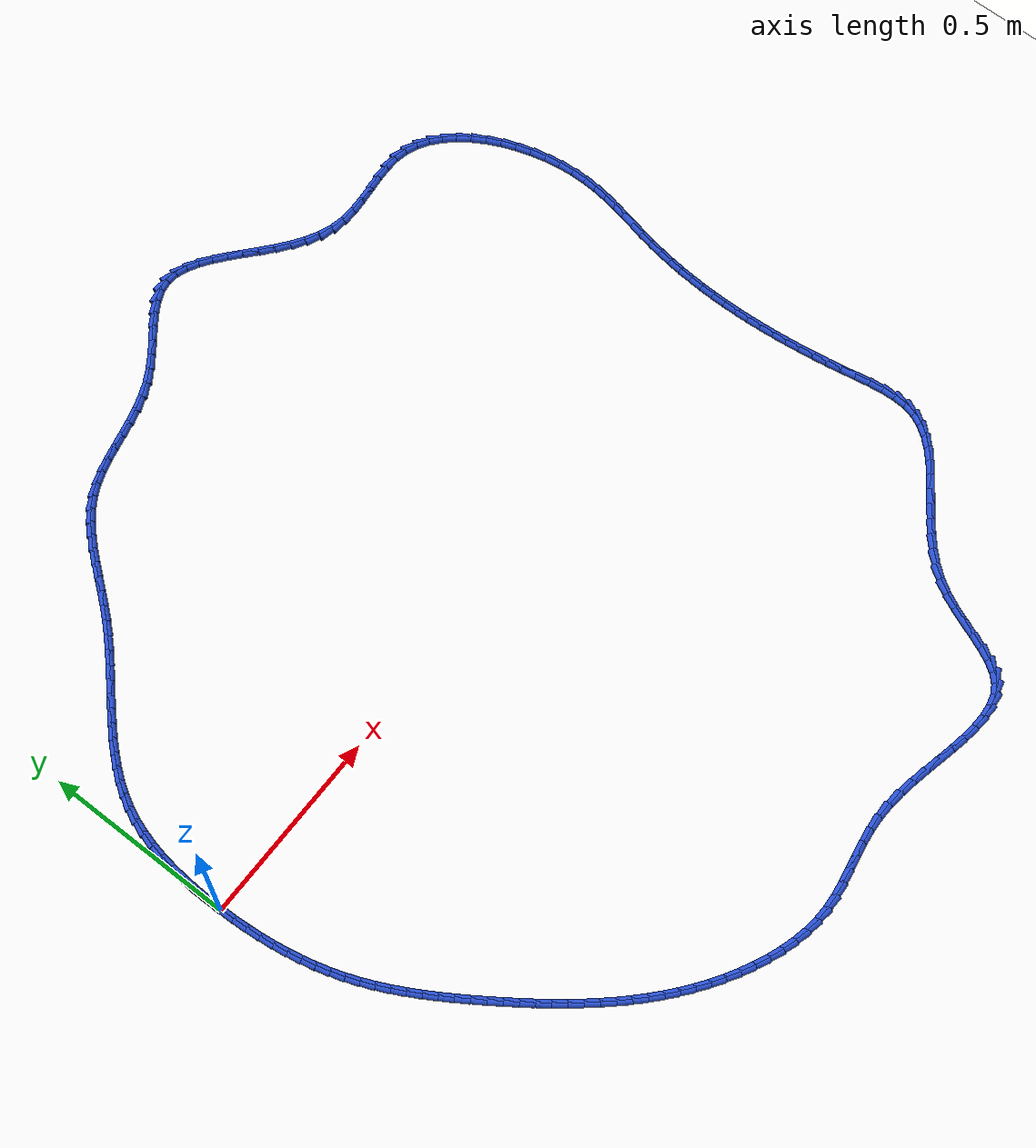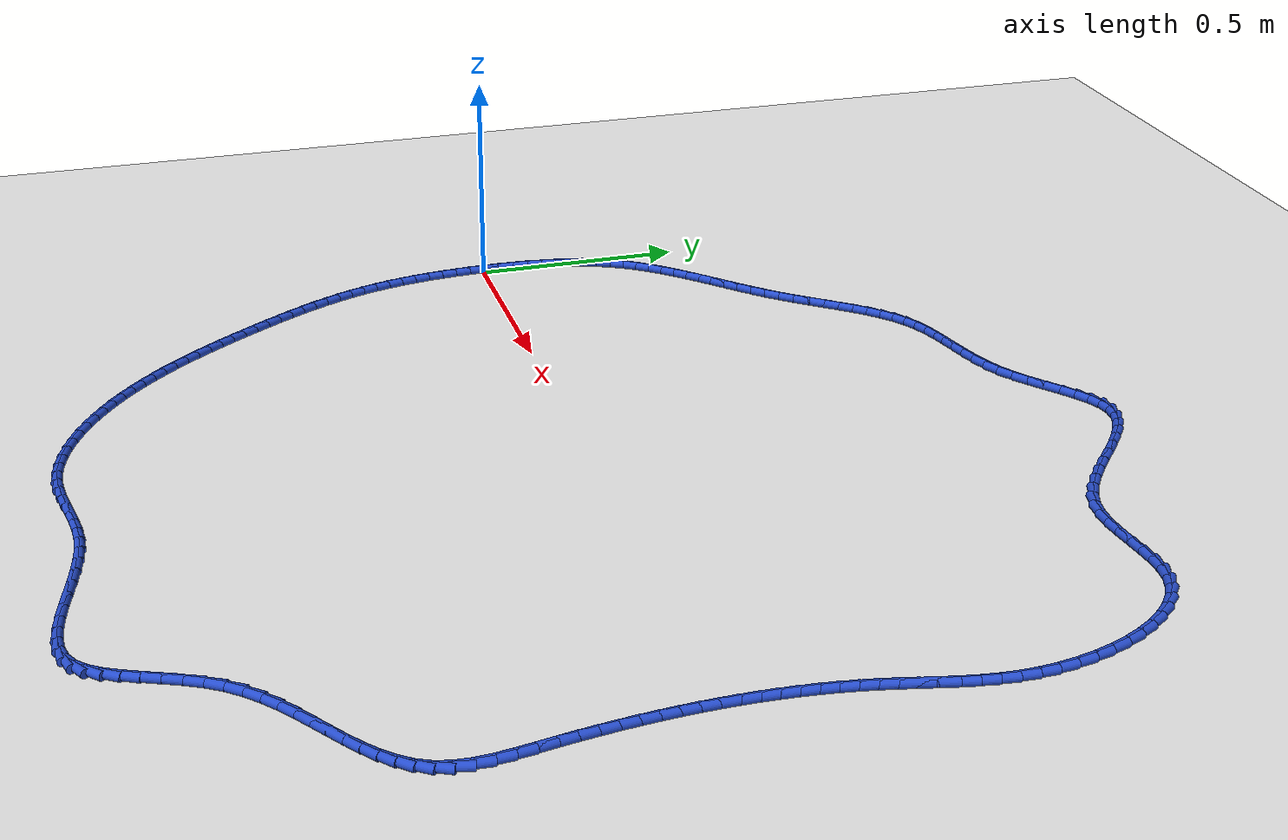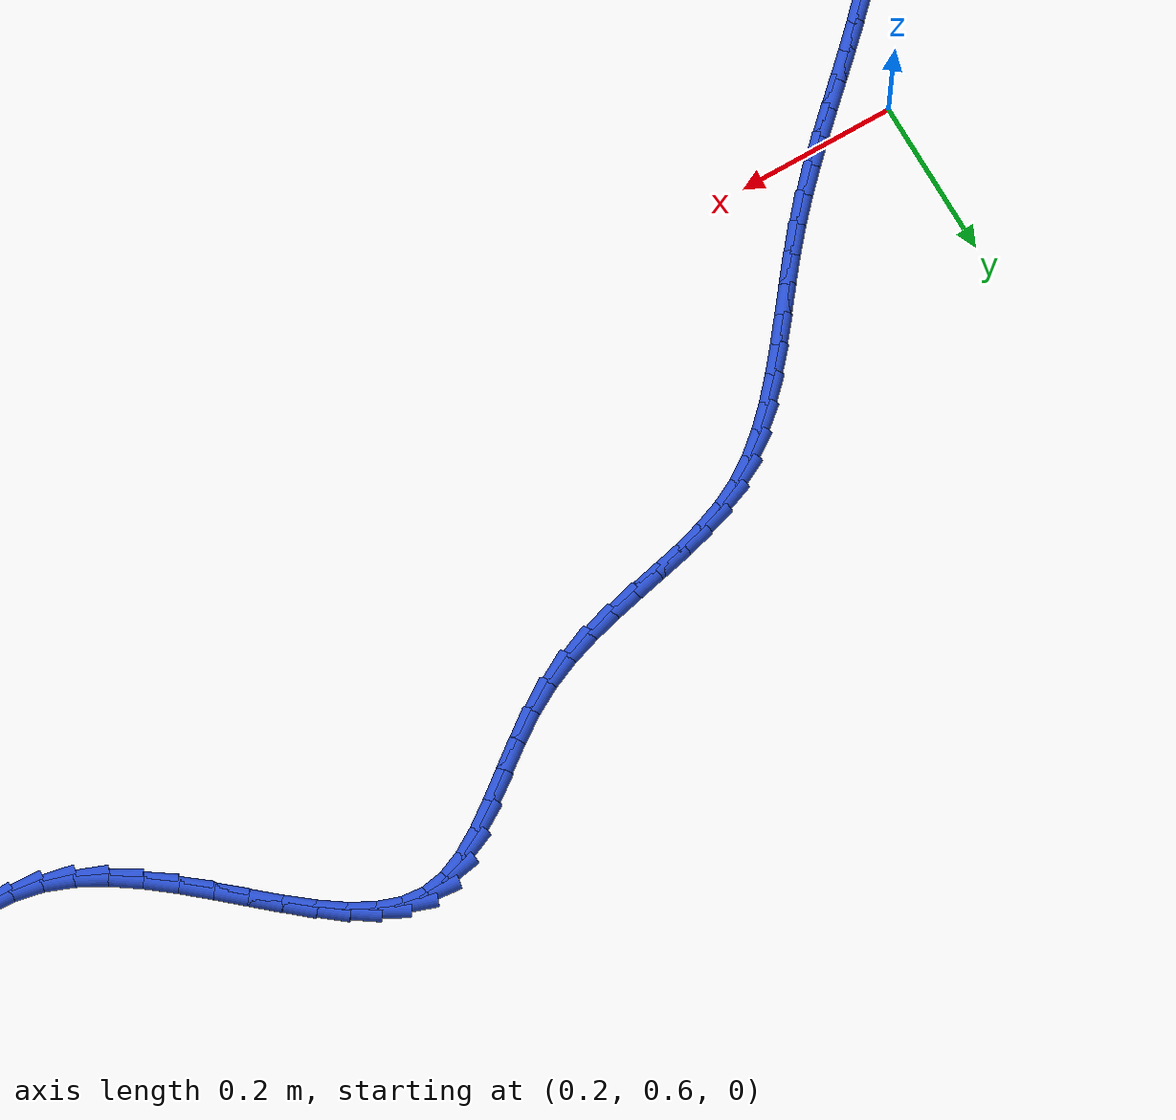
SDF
<sdf version="1.6">
 <world name="default">
  <light name="sun" type="directional">
   <pose>0 0 10 0 -0 0</pose>
   <diffuse>0.8 0.8 0.8 1</diffuse>
   <specular>0.2 0.2 0.2 1</specular>
   <attenuation>
    <range>1000</range>
    <constant>0.9</constant>
    <linear>0.01</linear>
    <quadratic>0.001</quadratic>
   </attenuation>
   <direction>-0.5 0.1 -0.9</direction>
  </light>
  <model name="ground_plane">
   <static>1</static>
   <link name="link">
    <collision name="collision">
     <geometry><plane><normal>0 0 1</normal><size>100 100</size></plane></geometry>
     <surface><friction><ode><mu>100</mu><mu2>50</mu2></ode></friction></surface>
    </collision>
    <visual name="visual">
     <cast_shadows>0</cast_shadows>
     <geometry><plane><normal>0 0 1</normal><size>100 100</size></plane></geometry>
     <material>
      <script><uri>file://media/materials/scripts/gazebo.material</uri><name>Gazebo/WhiteGlow</name></script>
     </material>
    </visual>
   </link>
  </model>
  <gravity>0 0 -9.8</gravity>
  <magnetic_field>6e-06 2.3e-05 -4.2e-05</magnetic_field>
  <atmosphere type="adiabatic"/>
  <physics name="default_physics" default="0" type="ode">
   <max_step_size>0.001</max_step_size>
   <real_time_factor>1</real_time_factor>
   <real_time_update_rate>1000</real_time_update_rate>
  </physics>
  <scene><ambient>0.4 0.4 0.4 1</ambient><background>0.7 0.7 0.7 1</background><shadows>1</shadows></scene>
  <spherical_coordinates>
   <surface_model>EARTH_WGS84</surface_model>
   <latitude_deg>0</latitude_deg>
   <longitude_deg>0</longitude_deg>
   <elevation>0</elevation>
   <heading_deg>0</heading_deg>
  </spherical_coordinates>
  <model name="line">
   <link name="link_0">
    <pose>-9.974659986866641e-18 -1.3877787807814457e-17 0.01 0 1.57 -1.5626560660773847</pose>
    <collision name="collision">
     <geometry><cylinder><radius>0.01</radius><length>0.08</length></cylinder></geometry>
    </collision>
    <visual name="visual">
     <material>
      <script><name>Gazebo/Blue</name><uri>file://media/materials/scripts/gazebo.material</uri></script>
     </material>
     <geometry><cylinder><radius>0.01</radius><length>0.08</length></cylinder></geometry>
    </visual>
   </link>
   <link name="link_1">
    <pose>-0.00030532635874819746 0.03750735084304829 0.01 0 1.57 1.549180423849574</pose>
    <collision name="collision">
     <geometry><cylinder><radius>0.01</radius><length>0.08</length></cylinder></geometry>
    </collision>
    <visual name="visual">
     <material>
      <script><name>Gazebo/Blue</name><uri>file://media/materials/scripts/gazebo.material</uri></script>
     </material>
     <geometry><cylinder><radius>0.01</radius><length>0.08</length></cylinder></geometry>
    </visual>
   </link>
   <link name="link_2">
    <pose>0.0005069069783849129 0.07507722847647917 0.01 0 1.57 1.5143218891924144</pose>
    <collision name="collision">
     <geometry><cylinder><radius>0.01</radius><length>0.08</length></cylinder></geometry>
    </collision>
    <visual name="visual">
     <material>
      <script><name>Gazebo/Blue</name><uri>file://media/materials/scripts/gazebo.material</uri></script>
     </material>
     <geometry><cylinder><radius>0.01</radius><length>0.08</length></cylinder></geometry>
    </visual>
   </link>
   <link name="link_3">
    <pose>0.002622778778997677 0.11250339834736747 0.01 0 1.57 1.473853161207346</pose>
    <collision name="collision">
     <geometry><cylinder><radius>0.01</radius><length>0.08</length></cylinder></geometry>
    </collision>
    <visual name="visual">
     <material>
      <script><name>Gazebo/Blue</name><uri>file://media/materials/scripts/gazebo.material</uri></script>
     </material>
     <geometry><cylinder><radius>0.01</radius><length>0.08</length></cylinder></geometry>
    </visual>
   </link>
   <link name="link_4">
    <pose>0.0062283678106884455 0.14957962590278812 0.01 0 1.57 1.4271759812119489</pose>
    <collision name="collision">
     <geometry><cylinder><radius>0.01</radius><length>0.08</length></cylinder></geometry>
    </collision>
    <visual name="visual">
     <material>
      <script><name>Gazebo/Blue</name><uri>file://media/materials/scripts/gazebo.material</uri></script>
     </material>
     <geometry><cylinder><radius>0.01</radius><length>0.08</length></cylinder></geometry>
    </visual>
   </link>
   <link name="link_5">
    <pose>0.01150975284105557 0.1860996765898159 0.01 0 1.57 1.373623108460975</pose>
    <collision name="collision">
     <geometry><cylinder><radius>0.01</radius><length>0.08</length></cylinder></geometry>
    </collision>
    <visual name="visual">
     <material>
      <script><name>Gazebo/Blue</name><uri>file://media/materials/scripts/gazebo.material</uri></script>
     </material>
     <geometry><cylinder><radius>0.01</radius><length>0.08</length></cylinder></geometry>
    </visual>
   </link>
   <link name="link_6">
    <pose>0.018653012637697402 0.22185731585552562 0.01 0 1.57 1.3124992903946913</pose>
    <collision name="collision">
     <geometry><cylinder><radius>0.01</radius><length>0.08</length></cylinder></geometry>
    </collision>
    <visual name="visual">
     <material>
      <script><name>Gazebo/Blue</name><uri>file://media/materials/scripts/gazebo.material</uri></script>
     </material>
     <geometry><cylinder><radius>0.01</radius><length>0.08</length></cylinder></geometry>
    </visual>
   </link>
   <link name="link_7">
    <pose>0.02784422596821229 0.2566463091469922 0.01 0 1.57 1.2431525621845227</pose>
    <collision name="collision">
     <geometry><cylinder><radius>0.01</radius><length>0.08</length></cylinder></geometry>
    </collision>
    <visual name="visual">
     <material>
      <script><name>Gazebo/Blue</name><uri>file://media/materials/scripts/gazebo.material</uri></script>
     </material>
     <geometry><cylinder><radius>0.01</radius><length>0.08</length></cylinder></geometry>
    </visual>
   </link>
   <link name="link_8">
    <pose>0.0392694716001986 0.2902604219112905 0.01 0 1.57 1.1650866859020828</pose>
    <collision name="collision">
     <geometry><cylinder><radius>0.01</radius><length>0.08</length></cylinder></geometry>
    </collision>
    <visual name="visual">
     <material>
      <script><name>Gazebo/Blue</name><uri>file://media/materials/scripts/gazebo.material</uri></script>
     </material>
     <geometry><cylinder><radius>0.01</radius><length>0.08</length></cylinder></geometry>
    </visual>
   </link>
   <link name="link_9">
    <pose>0.05311482830125466 0.3224934195954953 0.01 0 1.57 1.08047660575736</pose>
    <collision name="collision">
     <geometry><cylinder><radius>0.01</radius><length>0.08</length></cylinder></geometry>
    </collision>
    <visual name="visual">
     <material>
      <script><name>Gazebo/Blue</name><uri>file://media/materials/scripts/gazebo.material</uri></script>
     </material>
     <geometry><cylinder><radius>0.01</radius><length>0.08</length></cylinder></geometry>
    </visual>
   </link>
   <link name="link_10">
    <pose>0.06950334716734584 0.35319509186845555 0.01 0 1.57 1.0016460030227365</pose>
    <collision name="collision">
     <geometry><cylinder><radius>0.01</radius><length>0.08</length></cylinder></geometry>
    </collision>
    <visual name="visual">
     <material>
      <script><name>Gazebo/Blue</name><uri>file://media/materials/scripts/gazebo.material</uri></script>
     </material>
     <geometry><cylinder><radius>0.01</radius><length>0.08</length></cylinder></geometry>
    </visual>
   </link>
   <link name="link_11">
    <pose>0.0882466670813143 0.38249203740114734 0.01 0 1.57 0.933342731683411</pose>
    <collision name="collision">
     <geometry><cylinder><radius>0.01</radius><length>0.08</length></cylinder></geometry>
    </collision>
    <visual name="visual">
     <material>
      <script><name>Gazebo/Blue</name><uri>file://media/materials/scripts/gazebo.material</uri></script>
     </material>
     <geometry><cylinder><radius>0.01</radius><length>0.08</length></cylinder></geometry>
    </visual>
   </link>
   <link name="link_12">
    <pose>0.10906041836883569 0.4105961952326668 0.01 0 1.57 0.8761231536649013</pose>
    <collision name="collision">
     <geometry><cylinder><radius>0.01</radius><length>0.08</length></cylinder></geometry>
    </collision>
    <visual name="visual">
     <material>
      <script><name>Gazebo/Blue</name><uri>file://media/materials/scripts/gazebo.material</uri></script>
     </material>
     <geometry><cylinder><radius>0.01</radius><length>0.08</length></cylinder></geometry>
    </visual>
   </link>
   <link name="link_13">
    <pose>0.13166020420967026 0.4377195285316511 0.01 0 1.57 0.8300223372190902</pose>
    <collision name="collision">
     <geometry><cylinder><radius>0.01</radius><length>0.08</length></cylinder></geometry>
    </collision>
    <visual name="visual">
     <material>
      <script><name>Gazebo/Blue</name><uri>file://media/materials/scripts/gazebo.material</uri></script>
     </material>
     <geometry><cylinder><radius>0.01</radius><length>0.08</length></cylinder></geometry>
    </visual>
   </link>
   <link name="link_14">
    <pose>0.15576162778357813 0.46407400046673697 0.01 0 1.57 0.7947669130897883</pose>
    <collision name="collision">
     <geometry><cylinder><radius>0.01</radius><length>0.08</length></cylinder></geometry>
    </collision>
    <visual name="visual">
     <material>
      <script><name>Gazebo/Blue</name><uri>file://media/materials/scripts/gazebo.material</uri></script>
     </material>
     <geometry><cylinder><radius>0.01</radius><length>0.08</length></cylinder></geometry>
    </visual>
   </link>
   <link name="link_15">
    <pose>0.18108029227031985 0.48987157420656186 0.01 0 1.57 0.7699486038070023</pose>
    <collision name="collision">
     <geometry><cylinder><radius>0.01</radius><length>0.08</length></cylinder></geometry>
    </collision>
    <visual name="visual">
     <material>
      <script><name>Gazebo/Blue</name><uri>file://media/materials/scripts/gazebo.material</uri></script>
     </material>
     <geometry><cylinder><radius>0.01</radius><length>0.08</length></cylinder></geometry>
    </visual>
   </link>
   <link name="link_16">
    <pose>0.20733180084965544 0.5153242129197625 0.01 0 1.57 0.7551450369967525</pose>
    <collision name="collision">
     <geometry><cylinder><radius>0.01</radius><length>0.08</length></cylinder></geometry>
    </collision>
    <visual name="visual">
     <material>
      <script><name>Gazebo/Blue</name><uri>file://media/materials/scripts/gazebo.material</uri></script>
     </material>
     <geometry><cylinder><radius>0.01</radius><length>0.08</length></cylinder></geometry>
    </visual>
   </link>
   <link name="link_17">
    <pose>0.23423175670134516 0.5406438797749761 0.01 0 1.57 0.7499922712167783</pose>
    <collision name="collision">
     <geometry><cylinder><radius>0.01</radius><length>0.08</length></cylinder></geometry>
    </collision>
    <visual name="visual">
     <material>
      <script><name>Gazebo/Blue</name><uri>file://media/materials/scripts/gazebo.material</uri></script>
     </material>
     <geometry><cylinder><radius>0.01</radius><length>0.08</length></cylinder></geometry>
    </visual>
   </link>
   <link name="link_18">
    <pose>0.26149576300514943 0.5660425379408398 0.01 0 1.57 0.7542194108745286</pose>
    <collision name="collision">
     <geometry><cylinder><radius>0.01</radius><length>0.08</length></cylinder></geometry>
    </collision>
    <visual name="visual">
     <material>
      <script><name>Gazebo/Blue</name><uri>file://media/materials/scripts/gazebo.material</uri></script>
     </material>
     <geometry><cylinder><radius>0.01</radius><length>0.08</length></cylinder></geometry>
    </visual>
   </link>
   <link name="link_19">
    <pose>0.2888394229408282 0.5917321505859903 0.01 0 1.57 0.7676546520729435</pose>
    <collision name="collision">
     <geometry><cylinder><radius>0.01</radius><length>0.08</length></cylinder></geometry>
    </collision>
    <visual name="visual">
     <material>
      <script><name>Gazebo/Blue</name><uri>file://media/materials/scripts/gazebo.material</uri></script>
     </material>
     <geometry><cylinder><radius>0.01</radius><length>0.08</length></cylinder></geometry>
    </visual>
   </link>
   <link name="link_20">
    <pose>0.31597833968814204 0.6179246808790648 0.01 0 1.57 0.7902085799642066</pose>
    <collision name="collision">
     <geometry><cylinder><radius>0.01</radius><length>0.08</length></cylinder></geometry>
    </collision>
    <visual name="visual">
     <material>
      <script><name>Gazebo/Blue</name><uri>file://media/materials/scripts/gazebo.material</uri></script>
     </material>
     <geometry><cylinder><radius>0.01</radius><length>0.08</length></cylinder></geometry>
    </visual>
   </link>
   <link name="link_21">
    <pose>0.34262811642685087 0.6448320919887004 0.01 0 1.57 0.8218370101698297</pose>
    <collision name="collision">
     <geometry><cylinder><radius>0.01</radius><length>0.08</length></cylinder></geometry>
    </collision>
    <visual name="visual">
     <material>
      <script><name>Gazebo/Blue</name><uri>file://media/materials/scripts/gazebo.material</uri></script>
     </material>
     <geometry><cylinder><radius>0.01</radius><length>0.08</length></cylinder></geometry>
    </visual>
   </link>
   <link name="link_22">
    <pose>0.36850435633671547 0.6726663470835346 0.01 0 1.57 0.860241233107101</pose>
    <collision name="collision">
     <geometry><cylinder><radius>0.01</radius><length>0.08</length></cylinder></geometry>
    </collision>
    <visual name="visual">
     <material>
      <script><name>Gazebo/Blue</name><uri>file://media/materials/scripts/gazebo.material</uri></script>
     </material>
     <geometry><cylinder><radius>0.01</radius><length>0.08</length></cylinder></geometry>
    </visual>
   </link>
   <link name="link_23">
    <pose>0.39337820583742383 0.7015728128269176 0.01 0 1.57 0.8890972657792442</pose>
    <collision name="collision">
     <geometry><cylinder><radius>0.01</radius><length>0.08</length></cylinder></geometry>
    </collision>
    <visual name="visual">
     <material>
      <script><name>Gazebo/Blue</name><uri>file://media/materials/scripts/gazebo.material</uri></script>
     </material>
     <geometry><cylinder><radius>0.01</radius><length>0.08</length></cylinder></geometry>
    </visual>
   </link>
   <link name="link_24">
    <pose>0.41742746590059676 0.7312092758985341 0.01 0 1.57 0.9014537029326046</pose>
    <collision name="collision">
     <geometry><cylinder><radius>0.01</radius><length>0.08</length></cylinder></geometry>
    </collision>
    <visual name="visual">
     <material>
      <script><name>Gazebo/Blue</name><uri>file://media/materials/scripts/gazebo.material</uri></script>
     </material>
     <geometry><cylinder><radius>0.01</radius><length>0.08</length></cylinder></geometry>
    </visual>
   </link>
   <link name="link_25">
    <pose>0.4410107076216747 0.7610167790768834 0.01 0 1.57 0.8972642154509697</pose>
    <collision name="collision">
     <geometry><cylinder><radius>0.01</radius><length>0.08</length></cylinder></geometry>
    </collision>
    <visual name="visual">
     <material>
      <script><name>Gazebo/Blue</name><uri>file://media/materials/scripts/gazebo.material</uri></script>
     </material>
     <geometry><cylinder><radius>0.01</radius><length>0.08</length></cylinder></geometry>
    </visual>
   </link>
   <link name="link_26">
    <pose>0.4644873232608106 0.7904353805616003 0.01 0 1.57 0.8759630446148179</pose>
    <collision name="collision">
     <geometry><cylinder><radius>0.01</radius><length>0.08</length></cylinder></geometry>
    </collision>
    <visual name="visual">
     <material>
      <script><name>Gazebo/Blue</name><uri>file://media/materials/scripts/gazebo.material</uri></script>
     </material>
     <geometry><cylinder><radius>0.01</radius><length>0.08</length></cylinder></geometry>
    </visual>
   </link>
   <link name="link_27">
    <pose>0.48821670507815695 0.8189051385523197 0.01 0 1.57 0.8364124232769974</pose>
    <collision name="collision">
     <geometry><cylinder><radius>0.01</radius><length>0.08</length></cylinder></geometry>
    </collision>
    <visual name="visual">
     <material>
      <script><name>Gazebo/Blue</name><uri>file://media/materials/scripts/gazebo.material</uri></script>
     </material>
     <geometry><cylinder><radius>0.01</radius><length>0.08</length></cylinder></geometry>
    </visual>
   </link>
   <link name="link_28">
    <pose>0.5125582453338667 0.8458661112486767 0.01 0 1.57 0.777015877273311</pose>
    <collision name="collision">
     <geometry><cylinder><radius>0.01</radius><length>0.08</length></cylinder></geometry>
    </collision>
    <visual name="visual">
     <material>
      <script><name>Gazebo/Blue</name><uri>file://media/materials/scripts/gazebo.material</uri></script>
     </material>
     <geometry><cylinder><radius>0.01</radius><length>0.08</length></cylinder></geometry>
    </visual>
   </link>
   <link name="link_29">
    <pose>0.5378713362880929 0.8707583568503071 0.01 0 1.57 0.6960705561602372</pose>
    <collision name="collision">
     <geometry><cylinder><radius>0.01</radius><length>0.08</length></cylinder></geometry>
    </collision>
    <visual name="visual">
     <material>
      <script><name>Gazebo/Blue</name><uri>file://media/materials/scripts/gazebo.material</uri></script>
     </material>
     <geometry><cylinder><radius>0.01</radius><length>0.08</length></cylinder></geometry>
    </visual>
   </link>
   <link name="link_30">
    <pose>0.5645153702009881 0.8930219335568452 0.01 0 1.57 0.5925185780753299</pose>
    <collision name="collision">
     <geometry><cylinder><radius>0.01</radius><length>0.08</length></cylinder></geometry>
    </collision>
    <visual name="visual">
     <material>
      <script><name>Gazebo/Blue</name><uri>file://media/materials/scripts/gazebo.material</uri></script>
     </material>
     <geometry><cylinder><radius>0.01</radius><length>0.08</length></cylinder></geometry>
    </visual>
   </link>
   <link name="link_31">
    <pose>0.5928497393327049 0.9120968995679262 0.01 0 1.57 0.47000072901425355</pose>
    <collision name="collision">
     <geometry><cylinder><radius>0.01</radius><length>0.08</length></cylinder></geometry>
    </collision>
    <visual name="visual">
     <material>
      <script><name>Gazebo/Blue</name><uri>file://media/materials/scripts/gazebo.material</uri></script>
     </material>
     <geometry><cylinder><radius>0.01</radius><length>0.08</length></cylinder></geometry>
    </visual>
   </link>
   <link name="link_32">
    <pose>0.6231911719347277 0.927509340427059 0.01 0 1.57 0.36053438935371207</pose>
    <collision name="collision">
     <geometry><cylinder><radius>0.01</radius><length>0.08</length></cylinder></geometry>
    </collision>
    <visual name="visual">
     <material>
      <script><name>Gazebo/Blue</name><uri>file://media/materials/scripts/gazebo.material</uri></script>
     </material>
     <geometry><cylinder><radius>0.01</radius><length>0.08</length></cylinder></geometry>
    </visual>
   </link>
   <link name="link_33">
    <pose>0.6554221966028583 0.9396608581670598 0.01 0 1.57 0.28268333280211533</pose>
    <collision name="collision">
     <geometry><cylinder><radius>0.01</radius><length>0.08</length></cylinder></geometry>
    </collision>
    <visual name="visual">
     <material>
      <script><name>Gazebo/Blue</name><uri>file://media/materials/scripts/gazebo.material</uri></script>
     </material>
     <geometry><cylinder><radius>0.01</radius><length>0.08</length></cylinder></geometry>
    </visual>
   </link>
   <link name="link_34">
    <pose>0.6891720021524068 0.9494638869974044 0.01 0 1.57 0.2355085056326991</pose>
    <collision name="collision">
     <geometry><cylinder><radius>0.01</radius><length>0.08</length></cylinder></geometry>
    </collision>
    <visual name="visual">
     <material>
      <script><name>Gazebo/Blue</name><uri>file://media/materials/scripts/gazebo.material</uri></script>
     </material>
     <geometry><cylinder><radius>0.01</radius><length>0.08</length></cylinder></geometry>
    </visual>
   </link>
   <link name="link_35">
    <pose>0.7240666104640009 0.9578372469077019 0.01 0 1.57 0.21698126229757012</pose>
    <collision name="collision">
     <geometry><cylinder><radius>0.01</radius><length>0.08</length></cylinder></geometry>
    </collision>
    <visual name="visual">
     <material>
      <script><name>Gazebo/Blue</name><uri>file://media/materials/scripts/gazebo.material</uri></script>
     </material>
     <geometry><cylinder><radius>0.01</radius><length>0.08</length></cylinder></geometry>
    </visual>
   </link>
   <link name="link_36">
    <pose>0.7597320434182688 0.9656997578875618 0.01 0 1.57 0.225440373829663</pose>
    <collision name="collision">
     <geometry><cylinder><radius>0.01</radius><length>0.08</length></cylinder></geometry>
    </collision>
    <visual name="visual">
     <material>
      <script><name>Gazebo/Blue</name><uri>file://media/materials/scripts/gazebo.material</uri></script>
     </material>
     <geometry><cylinder><radius>0.01</radius><length>0.08</length></cylinder></geometry>
    </visual>
   </link>
   <link name="link_37">
    <pose>0.7957943228958384 0.9739702399265933 0.01 0 1.57 0.2599442628431979</pose>
    <collision name="collision">
     <geometry><cylinder><radius>0.01</radius><length>0.08</length></cylinder></geometry>
    </collision>
    <visual name="visual">
     <material>
      <script><name>Gazebo/Blue</name><uri>file://media/materials/scripts/gazebo.material</uri></script>
     </material>
     <geometry><cylinder><radius>0.01</radius><length>0.08</length></cylinder></geometry>
    </visual>
   </link>
   <link name="link_38">
    <pose>0.8318794707773378 0.9835675130144047 0.01 0 1.57 0.32002527751777865</pose>
    <collision name="collision">
     <geometry><cylinder><radius>0.01</radius><length>0.08</length></cylinder></geometry>
    </collision>
    <visual name="visual">
     <material>
      <script><name>Gazebo/Blue</name><uri>file://media/materials/scripts/gazebo.material</uri></script>
     </material>
     <geometry><cylinder><radius>0.01</radius><length>0.08</length></cylinder></geometry>
    </visual>
   </link>
   <link name="link_39">
    <pose>0.8676135089433947 0.9954103971406059 0.01 0 1.57 0.40497574484682314</pose>
    <collision name="collision">
     <geometry><cylinder><radius>0.01</radius><length>0.08</length></cylinder></geometry>
    </collision>
    <visual name="visual">
     <material>
      <script><name>Gazebo/Blue</name><uri>file://media/materials/scripts/gazebo.material</uri></script>
     </material>
     <geometry><cylinder><radius>0.01</radius><length>0.08</length></cylinder></geometry>
    </visual>
   </link>
   <link name="link_40">
    <pose>0.9026224592746372 1.0104177122948055 0.01 0 1.57 0.5106003617391673</pose>
    <collision name="collision">
     <geometry><cylinder><radius>0.01</radius><length>0.08</length></cylinder></geometry>
    </collision>
    <visual name="visual">
     <material>
      <script><name>Gazebo/Blue</name><uri>file://media/materials/scripts/gazebo.material</uri></script>
     </material>
     <geometry><cylinder><radius>0.01</radius><length>0.08</length></cylinder></geometry>
    </visual>
   </link>
   <link name="link_41">
    <pose>0.9365493048600816 1.029421739336805 0.01 0 1.57 0.5996888038411738</pose>
    <collision name="collision">
     <geometry><cylinder><radius>0.01</radius><length>0.08</length></cylinder></geometry>
    </collision>
    <visual name="visual">
     <material>
      <script><name>Gazebo/Blue</name><uri>file://media/materials/scripts/gazebo.material</uri></script>
     </material>
     <geometry><cylinder><radius>0.01</radius><length>0.08</length></cylinder></geometry>
    </visual>
   </link>
   <link name="link_42">
    <pose>0.9693173347401967 1.0518245878459385 0.01 0 1.57 0.6476635759384094</pose>
    <collision name="collision">
     <geometry><cylinder><radius>0.01</radius><length>0.08</length></cylinder></geometry>
    </collision>
    <visual name="visual">
     <material>
      <script><name>Gazebo/Blue</name><uri>file://media/materials/scripts/gazebo.material</uri></script>
     </material>
     <geometry><cylinder><radius>0.01</radius><length>0.08</length></cylinder></geometry>
    </visual>
   </link>
   <link name="link_43">
    <pose>1.001080038344064 1.0758538436968534 0.01 0 1.57 0.6570278179525036</pose>
    <collision name="collision">
     <geometry><cylinder><radius>0.01</radius><length>0.08</length></cylinder></geometry>
    </collision>
    <visual name="visual">
     <material>
      <script><name>Gazebo/Blue</name><uri>file://media/materials/scripts/gazebo.material</uri></script>
     </material>
     <geometry><cylinder><radius>0.01</radius><length>0.08</length></cylinder></geometry>
    </visual>
   </link>
   <link name="link_44">
    <pose>1.0319977232096125 1.099702305548983 0.01 0 1.57 0.6260400267948361</pose>
    <collision name="collision">
     <geometry><cylinder><radius>0.01</radius><length>0.08</length></cylinder></geometry>
    </collision>
    <visual name="visual">
     <material>
      <script><name>Gazebo/Blue</name><uri>file://media/materials/scripts/gazebo.material</uri></script>
     </material>
     <geometry><cylinder><radius>0.01</radius><length>0.08</length></cylinder></geometry>
    </visual>
   </link>
   <link name="link_45">
    <pose>1.0622306968747692 1.1215627720617598 0.01 0 1.57 0.5463415337071155</pose>
    <collision name="collision">
     <geometry><cylinder><radius>0.01</radius><length>0.08</length></cylinder></geometry>
    </collision>
    <visual name="visual">
     <material>
      <script><name>Gazebo/Blue</name><uri>file://media/materials/scripts/gazebo.material</uri></script>
     </material>
     <geometry><cylinder><radius>0.01</radius><length>0.08</length></cylinder></geometry>
    </visual>
   </link>
   <link name="link_46">
    <pose>1.091939266877463 1.139628041894617 0.01 0 1.57 0.40162442077815236</pose>
    <collision name="collision">
     <geometry><cylinder><radius>0.01</radius><length>0.08</length></cylinder></geometry>
    </collision>
    <visual name="visual">
     <material>
      <script><name>Gazebo/Blue</name><uri>file://media/materials/scripts/gazebo.material</uri></script>
     </material>
     <geometry><cylinder><radius>0.01</radius><length>0.08</length></cylinder></geometry>
    </visual>
   </link>
   <link name="link_47">
    <pose>1.1212837407556215 1.152090913706987 0.01 0 1.57 0.1722717982515701</pose>
    <collision name="collision">
     <geometry><cylinder><radius>0.01</radius><length>0.08</length></cylinder></geometry>
    </collision>
    <visual name="visual">
     <material>
      <script><name>Gazebo/Blue</name><uri>file://media/materials/scripts/gazebo.material</uri></script>
     </material>
     <geometry><cylinder><radius>0.01</radius><length>0.08</length></cylinder></geometry>
    </visual>
   </link>
   <link name="link_48">
    <pose>1.1504240829267782 1.1571612306065244 0.01 0 1.57 -0.10327528615485557</pose>
    <collision name="collision">
     <geometry><cylinder><radius>0.01</radius><length>0.08</length></cylinder></geometry>
    </collision>
    <visual name="visual">
     <material>
      <script><name>Gazebo/Blue</name><uri>file://media/materials/scripts/gazebo.material</uri></script>
     </material>
     <geometry><cylinder><radius>0.01</radius><length>0.08</length></cylinder></geometry>
    </visual>
   </link>
   <link name="link_49">
    <pose>1.179498133059951 1.1541478788803008 0.01 0 1.57 -0.33209387217334396</pose>
    <collision name="collision">
     <geometry><cylinder><radius>0.01</radius><length>0.08</length></cylinder></geometry>
    </collision>
    <visual name="visual">
     <material>
      <script><name>Gazebo/Blue</name><uri>file://media/materials/scripts/gazebo.material</uri></script>
     </material>
     <geometry><cylinder><radius>0.01</radius><length>0.08</length></cylinder></geometry>
    </visual>
   </link>
   <link name="link_50">
    <pose>1.208608522895355 1.144108692786064 0.01 0 1.57 -0.49667641972006243</pose>
    <collision name="collision">
     <geometry><cylinder><radius>0.01</radius><length>0.08</length></cylinder></geometry>
    </collision>
    <visual name="visual">
     <material>
      <script><name>Gazebo/Blue</name><uri>file://media/materials/scripts/gazebo.material</uri></script>
     </material>
     <geometry><cylinder><radius>0.01</radius><length>0.08</length></cylinder></geometry>
    </visual>
   </link>
   <link name="link_51">
    <pose>1.2378547460610079 1.1282573917796943 0.01 0 1.57 -0.6064473536490044</pose>
    <collision name="collision">
     <geometry><cylinder><radius>0.01</radius><length>0.08</length></cylinder></geometry>
    </collision>
    <visual name="visual">
     <material>
      <script><name>Gazebo/Blue</name><uri>file://media/materials/scripts/gazebo.material</uri></script>
     </material>
     <geometry><cylinder><radius>0.01</radius><length>0.08</length></cylinder></geometry>
    </visual>
   </link>
   <link name="link_52">
    <pose>1.2673362961849277 1.1078076953170704 0.01 0 1.57 -0.6743579098500069</pose>
    <collision name="collision">
     <geometry><cylinder><radius>0.01</radius><length>0.08</length></cylinder></geometry>
    </collision>
    <visual name="visual">
     <material>
      <script><name>Gazebo/Blue</name><uri>file://media/materials/scripts/gazebo.material</uri></script>
     </material>
     <geometry><cylinder><radius>0.01</radius><length>0.08</length></cylinder></geometry>
    </visual>
   </link>
   <link name="link_53">
    <pose>1.2971526668951319 1.0839733228540716 0.01 0 1.57 -0.7100760065322824</pose>
    <collision name="collision">
     <geometry><cylinder><radius>0.01</radius><length>0.08</length></cylinder></geometry>
    </collision>
    <visual name="visual">
     <material>
      <script><name>Gazebo/Blue</name><uri>file://media/materials/scripts/gazebo.material</uri></script>
     </material>
     <geometry><cylinder><radius>0.01</radius><length>0.08</length></cylinder></geometry>
    </visual>
   </link>
   <link name="link_54">
    <pose>1.3274033518196393 1.0579679938465762 0.01 0 1.57 -0.7193106265227113</pose>
    <collision name="collision">
     <geometry><cylinder><radius>0.01</radius><length>0.08</length></cylinder></geometry>
    </collision>
    <visual name="visual">
     <material>
      <script><name>Gazebo/Blue</name><uri>file://media/materials/scripts/gazebo.material</uri></script>
     </material>
     <geometry><cylinder><radius>0.01</radius><length>0.08</length></cylinder></geometry>
    </visual>
   </link>
   <link name="link_55">
    <pose>1.3581878445864675 1.0310054277504646 0.01 0 1.57 -0.7045117779025492</pose>
    <collision name="collision">
     <geometry><cylinder><radius>0.01</radius><length>0.08</length></cylinder></geometry>
    </collision>
    <visual name="visual">
     <material>
      <script><name>Gazebo/Blue</name><uri>file://media/materials/scripts/gazebo.material</uri></script>
     </material>
     <geometry><cylinder><radius>0.01</radius><length>0.08</length></cylinder></geometry>
    </visual>
   </link>
   <link name="link_56">
    <pose>1.3896056388236342 1.0042993440216157 0.01 0 1.57 -0.6654825882840671</pose>
    <collision name="collision">
     <geometry><cylinder><radius>0.01</radius><length>0.08</length></cylinder></geometry>
    </collision>
    <visual name="visual">
     <material>
      <script><name>Gazebo/Blue</name><uri>file://media/materials/scripts/gazebo.material</uri></script>
     </material>
     <geometry><cylinder><radius>0.01</radius><length>0.08</length></cylinder></geometry>
    </visual>
   </link>
   <link name="link_57">
    <pose>1.4217562281591571 0.9790634621159078 0.01 0 1.57 -0.5997347675856455</pose>
    <collision name="collision">
     <geometry><cylinder><radius>0.01</radius><length>0.08</length></cylinder></geometry>
    </collision>
    <visual name="visual">
     <material>
      <script><name>Gazebo/Blue</name><uri>file://media/materials/scripts/gazebo.material</uri></script>
     </material>
     <geometry><cylinder><radius>0.01</radius><length>0.08</length></cylinder></geometry>
    </visual>
   </link>
   <link name="link_58">
    <pose>1.454739106221055 0.9565115014892205 0.01 0 1.57 -0.5028716586022546</pose>
    <collision name="collision">
     <geometry><cylinder><radius>0.01</radius><length>0.08</length></cylinder></geometry>
    </collision>
    <visual name="visual">
     <material>
      <script><name>Gazebo/Blue</name><uri>file://media/materials/scripts/gazebo.material</uri></script>
     </material>
     <geometry><cylinder><radius>0.01</radius><length>0.08</length></cylinder></geometry>
    </visual>
   </link>
   <link name="link_59">
    <pose>1.4886537666373454 0.9378571815974337 0.01 0 1.57 -0.3697193525450164</pose>
    <collision name="collision">
     <geometry><cylinder><radius>0.01</radius><length>0.08</length></cylinder></geometry>
    </collision>
    <visual name="visual">
     <material>
      <script><name>Gazebo/Blue</name><uri>file://media/materials/scripts/gazebo.material</uri></script>
     </material>
     <geometry><cylinder><radius>0.01</radius><length>0.08</length></cylinder></geometry>
    </visual>
   </link>
   <link name="link_60">
    <pose>1.5235997030360469 0.924314221896426 0.01 0 1.57 -0.20212177524446714</pose>
    <collision name="collision">
     <geometry><cylinder><radius>0.01</radius><length>0.08</length></cylinder></geometry>
    </collision>
    <visual name="visual">
     <material>
      <script><name>Gazebo/Blue</name><uri>file://media/materials/scripts/gazebo.material</uri></script>
     </material>
     <geometry><cylinder><radius>0.01</radius><length>0.08</length></cylinder></geometry>
    </visual>
   </link>
   <link name="link_61">
    <pose>1.5596470012927166 0.9169274112970391 0.01 0 1.57 -0.052382942479392715</pose>
    <collision name="collision">
     <geometry><cylinder><radius>0.01</radius><length>0.08</length></cylinder></geometry>
    </collision>
    <visual name="visual">
     <material>
      <script><name>Gazebo/Blue</name><uri>file://media/materials/scripts/gazebo.material</uri></script>
     </material>
     <geometry><cylinder><radius>0.01</radius><length>0.08</length></cylinder></geometry>
    </visual>
   </link>
   <link name="link_62">
    <pose>1.5965611785759957 0.914991967479504 0.01 0 1.57 0.04750513816031851</pose>
    <collision name="collision">
     <geometry><cylinder><radius>0.01</radius><length>0.08</length></cylinder></geometry>
    </collision>
    <visual name="visual">
     <material>
      <script><name>Gazebo/Blue</name><uri>file://media/materials/scripts/gazebo.material</uri></script>
     </material>
     <geometry><cylinder><radius>0.01</radius><length>0.08</length></cylinder></geometry>
    </visual>
   </link>
   <link name="link_63">
    <pose>1.6339276284961053 0.9167684023627353 0.01 0 1.57 0.09954094323917025</pose>
    <collision name="collision">
     <geometry><cylinder><radius>0.01</radius><length>0.08</length></cylinder></geometry>
    </collision>
    <visual name="visual">
     <material>
      <script><name>Gazebo/Blue</name><uri>file://media/materials/scripts/gazebo.material</uri></script>
     </material>
     <geometry><cylinder><radius>0.01</radius><length>0.08</length></cylinder></geometry>
    </visual>
   </link>
   <link name="link_64">
    <pose>1.6713293993138387 0.9205037551883966 0.01 0 1.57 0.10606441386828748</pose>
    <collision name="collision">
     <geometry><cylinder><radius>0.01</radius><length>0.08</length></cylinder></geometry>
    </collision>
    <visual name="visual">
     <material>
      <script><name>Gazebo/Blue</name><uri>file://media/materials/scripts/gazebo.material</uri></script>
     </material>
     <geometry><cylinder><radius>0.01</radius><length>0.08</length></cylinder></geometry>
    </visual>
   </link>
   <link name="link_65">
    <pose>1.7083495392899866 0.9244450651981511 0.01 0 1.57 0.06600567359334854</pose>
    <collision name="collision">
     <geometry><cylinder><radius>0.01</radius><length>0.08</length></cylinder></geometry>
    </collision>
    <visual name="visual">
     <material>
      <script><name>Gazebo/Blue</name><uri>file://media/materials/scripts/gazebo.material</uri></script>
     </material>
     <geometry><cylinder><radius>0.01</radius><length>0.08</length></cylinder></geometry>
    </visual>
   </link>
   <link name="link_66">
    <pose>1.7445710966853414 0.9268393716336634 0.01 0 1.57 -0.02586571784299574</pose>
    <collision name="collision">
     <geometry><cylinder><radius>0.01</radius><length>0.08</length></cylinder></geometry>
    </collision>
    <visual name="visual">
     <material>
      <script><name>Gazebo/Blue</name><uri>file://media/materials/scripts/gazebo.material</uri></script>
     </material>
     <geometry><cylinder><radius>0.01</radius><length>0.08</length></cylinder></geometry>
    </visual>
   </link>
   <link name="link_67">
    <pose>1.7795771197606944 0.9259337137365963 0.01 0 1.57 -0.17655309258958518</pose>
    <collision name="collision">
     <geometry><cylinder><radius>0.01</radius><length>0.08</length></cylinder></geometry>
    </collision>
    <visual name="visual">
     <material>
      <script><name>Gazebo/Blue</name><uri>file://media/materials/scripts/gazebo.material</uri></script>
     </material>
     <geometry><cylinder><radius>0.01</radius><length>0.08</length></cylinder></geometry>
    </visual>
   </link>
   <link name="link_68">
    <pose>1.812951234125275 0.9199794145437403 0.01 0 1.57 -0.36612464667484435</pose>
    <collision name="collision">
     <geometry><cylinder><radius>0.01</radius><length>0.08</length></cylinder></geometry>
    </collision>
    <visual name="visual">
     <material>
      <script><name>Gazebo/Blue</name><uri>file://media/materials/scripts/gazebo.material</uri></script>
     </material>
     <geometry><cylinder><radius>0.01</radius><length>0.08</length></cylinder></geometry>
    </visual>
   </link>
   <link name="link_69">
    <pose>1.8443720181697452 0.9079323253043804 0.01 0 1.57 -0.5427850114803708</pose>
    <collision name="collision">
     <geometry><cylinder><radius>0.01</radius><length>0.08</length></cylinder></geometry>
    </collision>
    <visual name="visual">
     <material>
      <script><name>Gazebo/Blue</name><uri>file://media/materials/scripts/gazebo.material</uri></script>
     </material>
     <geometry><cylinder><radius>0.01</radius><length>0.08</length></cylinder></geometry>
    </visual>
   </link>
   <link name="link_70">
    <pose>1.8737177898526396 0.8902303197909393 0.01 0 1.57 -0.6966135162665091</pose>
    <collision name="collision">
     <geometry><cylinder><radius>0.01</radius><length>0.08</length></cylinder></geometry>
    </collision>
    <visual name="visual">
     <material>
      <script><name>Gazebo/Blue</name><uri>file://media/materials/scripts/gazebo.material</uri></script>
     </material>
     <geometry><cylinder><radius>0.01</radius><length>0.08</length></cylinder></geometry>
    </visual>
   </link>
   <link name="link_71">
    <pose>1.9008921104196952 0.8674985712708231 0.01 0 1.57 -0.8282191999990347</pose>
    <collision name="collision">
     <geometry><cylinder><radius>0.01</radius><length>0.08</length></cylinder></geometry>
    </collision>
    <visual name="visual">
     <material>
      <script><name>Gazebo/Blue</name><uri>file://media/materials/scripts/gazebo.material</uri></script>
     </material>
     <geometry><cylinder><radius>0.01</radius><length>0.08</length></cylinder></geometry>
    </visual>
   </link>
   <link name="link_72">
    <pose>1.9257985411166496 0.84036225301144 0.01 0 1.57 -0.9407752272063327</pose>
    <collision name="collision">
     <geometry><cylinder><radius>0.01</radius><length>0.08</length></cylinder></geometry>
    </collision>
    <visual name="visual">
     <material>
      <script><name>Gazebo/Blue</name><uri>file://media/materials/scripts/gazebo.material</uri></script>
     </material>
     <geometry><cylinder><radius>0.01</radius><length>0.08</length></cylinder></geometry>
    </visual>
   </link>
   <link name="link_73">
    <pose>1.9483406431892392 0.8094465382801971 0.01 0 1.57 -1.0381962233080713</pose>
    <collision name="collision">
     <geometry><cylinder><radius>0.01</radius><length>0.08</length></cylinder></geometry>
    </collision>
    <visual name="visual">
     <material>
      <script><name>Gazebo/Blue</name><uri>file://media/materials/scripts/gazebo.material</uri></script>
     </material>
     <geometry><cylinder><radius>0.01</radius><length>0.08</length></cylinder></geometry>
    </visual>
   </link>
   <link name="link_74">
    <pose>1.9684219778832013 0.7753766003445011 0.01 0 1.57 -1.1242402497801183</pose>
    <collision name="collision">
     <geometry><cylinder><radius>0.01</radius><length>0.08</length></cylinder></geometry>
    </collision>
    <visual name="visual">
     <material>
      <script><name>Gazebo/Blue</name><uri>file://media/materials/scripts/gazebo.material</uri></script>
     </material>
     <geometry><cylinder><radius>0.01</radius><length>0.08</length></cylinder></geometry>
    </visual>
   </link>
   <link name="link_75">
    <pose>1.9859461064442727 0.7387776124717592 0.01 0 1.57 -1.2022275043584887</pose>
    <collision name="collision">
     <geometry><cylinder><radius>0.01</radius><length>0.08</length></cylinder></geometry>
    </collision>
    <visual name="visual">
     <material>
      <script><name>Gazebo/Blue</name><uri>file://media/materials/scripts/gazebo.material</uri></script>
     </material>
     <geometry><cylinder><radius>0.01</radius><length>0.08</length></cylinder></geometry>
    </visual>
   </link>
   <link name="link_76">
    <pose>2.00081659011819 0.7002747479293793 0.01 0 1.57 -1.275057210495377</pose>
    <collision name="collision">
     <geometry><cylinder><radius>0.01</radius><length>0.08</length></cylinder></geometry>
    </collision>
    <visual name="visual">
     <material>
      <script><name>Gazebo/Blue</name><uri>file://media/materials/scripts/gazebo.material</uri></script>
     </material>
     <geometry><cylinder><radius>0.01</radius><length>0.08</length></cylinder></geometry>
    </visual>
   </link>
   <link name="link_77">
    <pose>2.0129369901506906 0.6604931799847679 0.01 0 1.57 -1.3453433039297358</pose>
    <collision name="collision">
     <geometry><cylinder><radius>0.01</radius><length>0.08</length></cylinder></geometry>
    </collision>
    <visual name="visual">
     <material>
      <script><name>Gazebo/Blue</name><uri>file://media/materials/scripts/gazebo.material</uri></script>
     </material>
     <geometry><cylinder><radius>0.01</radius><length>0.08</length></cylinder></geometry>
    </visual>
   </link>
   <link name="link_78">
    <pose>2.0222108677875115 0.6200580819053322 0.01 0 1.57 -1.415594491852058</pose>
    <collision name="collision">
     <geometry><cylinder><radius>0.01</radius><length>0.08</length></cylinder></geometry>
    </collision>
    <visual name="visual">
     <material>
      <script><name>Gazebo/Blue</name><uri>file://media/materials/scripts/gazebo.material</uri></script>
     </material>
     <geometry><cylinder><radius>0.01</radius><length>0.08</length></cylinder></geometry>
    </visual>
   </link>
   <link name="link_79">
    <pose>2.02854178427439 0.5795946269584795 0.01 0 1.57 -1.48841998224274</pose>
    <collision name="collision">
     <geometry><cylinder><radius>0.01</radius><length>0.08</length></cylinder></geometry>
    </collision>
    <visual name="visual">
     <material>
      <script><name>Gazebo/Blue</name><uri>file://media/materials/scripts/gazebo.material</uri></script>
     </material>
     <geometry><cylinder><radius>0.01</radius><length>0.08</length></cylinder></geometry>
    </visual>
   </link>
   <link name="link_80">
    <pose>2.0318333008570635 0.5397279884116178 0.01 0 1.57 -1.5655318531445603</pose>
    <collision name="collision">
     <geometry><cylinder><radius>0.01</radius><length>0.08</length></cylinder></geometry>
    </collision>
    <visual name="visual">
     <material>
      <script><name>Gazebo/Blue</name><uri>file://media/materials/scripts/gazebo.material</uri></script>
     </material>
     <geometry><cylinder><radius>0.01</radius><length>0.08</length></cylinder></geometry>
    </visual>
   </link>
   <link name="link_81">
    <pose>2.03203706415749 0.5010229949887464 0.01 0 1.57 1.5035822298520551</pose>
    <collision name="collision">
     <geometry><cylinder><radius>0.01</radius><length>0.08</length></cylinder></geometry>
    </collision>
    <visual name="visual">
     <material>
      <script><name>Gazebo/Blue</name><uri>file://media/materials/scripts/gazebo.material</uri></script>
     </material>
     <geometry><cylinder><radius>0.01</radius><length>0.08</length></cylinder></geometry>
    </visual>
   </link>
   <link name="link_82">
    <pose>2.0295133193657384 0.46353170633591406 0.01 0 1.57 1.4430906243674748</pose>
    <collision name="collision">
     <geometry><cylinder><radius>0.01</radius><length>0.08</length></cylinder></geometry>
    </collision>
    <visual name="visual">
     <material>
      <script><name>Gazebo/Blue</name><uri>file://media/materials/scripts/gazebo.material</uri></script>
     </material>
     <geometry><cylinder><radius>0.01</radius><length>0.08</length></cylinder></geometry>
    </visual>
   </link>
   <link name="link_83">
    <pose>2.0248285634363623 0.4270473473029734 0.01 0 1.57 1.3966643913521437</pose>
    <collision name="collision">
     <geometry><cylinder><radius>0.01</radius><length>0.08</length></cylinder></geometry>
    </collision>
    <visual name="visual">
     <material>
      <script><name>Gazebo/Blue</name><uri>file://media/materials/scripts/gazebo.material</uri></script>
     </material>
     <geometry><cylinder><radius>0.01</radius><length>0.08</length></cylinder></geometry>
    </visual>
   </link>
   <link name="link_84">
    <pose>2.018550878321735 0.39136115365333807 0.01 0 1.57 1.3656548942596838</pose>
    <collision name="collision">
     <geometry><cylinder><radius>0.01</radius><length>0.08</length></cylinder></geometry>
    </collision>
    <visual name="visual">
     <material>
      <script><name>Gazebo/Blue</name><uri>file://media/materials/scripts/gazebo.material</uri></script>
     </material>
     <geometry><cylinder><radius>0.01</radius><length>0.08</length></cylinder></geometry>
    </visual>
   </link>
   <link name="link_85">
    <pose>2.01124834597423 0.35626436115042187 0.01 0 1.57 1.3509035658939388</pose>
    <collision name="collision">
     <geometry><cylinder><radius>0.01</radius><length>0.08</length></cylinder></geometry>
    </collision>
    <visual name="visual">
     <material>
      <script><name>Gazebo/Blue</name><uri>file://media/materials/scripts/gazebo.material</uri></script>
     </material>
     <geometry><cylinder><radius>0.01</radius><length>0.08</length></cylinder></geometry>
    </visual>
   </link>
   <link name="link_86">
    <pose>2.003489048346222 0.3215482055576393 0.01 0 1.57 1.3529144486788878</pose>
    <collision name="collision">
     <geometry><cylinder><radius>0.01</radius><length>0.08</length></cylinder></geometry>
    </collision>
    <visual name="visual">
     <material>
      <script><name>Gazebo/Blue</name><uri>file://media/materials/scripts/gazebo.material</uri></script>
     </material>
     <geometry><cylinder><radius>0.01</radius><length>0.08</length></cylinder></geometry>
    </visual>
   </link>
   <link name="link_87">
    <pose>1.9958410673900833 0.2870039226384032 0.01 0 1.57 1.3717891092663264</pose>
    <collision name="collision">
     <geometry><cylinder><radius>0.01</radius><length>0.08</length></cylinder></geometry>
    </collision>
    <visual name="visual">
     <material>
      <script><name>Gazebo/Blue</name><uri>file://media/materials/scripts/gazebo.material</uri></script>
     </material>
     <geometry><cylinder><radius>0.01</radius><length>0.08</length></cylinder></geometry>
    </visual>
   </link>
   <link name="link_88">
    <pose>1.9888672129436198 0.2524245407548305 0.01 0 1.57 1.4004895127071482</pose>
    <collision name="collision">
     <geometry><cylinder><radius>0.01</radius><length>0.08</length></cylinder></geometry>
    </collision>
    <visual name="visual">
     <material>
      <script><name>Gazebo/Blue</name><uri>file://media/materials/scripts/gazebo.material</uri></script>
     </material>
     <geometry><cylinder><radius>0.01</radius><length>0.08</length></cylinder></geometry>
    </visual>
   </link>
   <link name="link_89">
    <pose>1.9828927632292759 0.21768385261130643 0.01 0 1.57 1.4291640493108273</pose>
    <collision name="collision">
     <geometry><cylinder><radius>0.01</radius><length>0.08</length></cylinder></geometry>
    </collision>
    <visual name="visual">
     <material>
      <script><name>Gazebo/Blue</name><uri>file://media/materials/scripts/gazebo.material</uri></script>
     </material>
     <geometry><cylinder><radius>0.01</radius><length>0.08</length></cylinder></geometry>
    </visual>
   </link>
   <link name="link_90">
    <pose>1.9779141414615193 0.18276746658938886 0.01 0 1.57 1.4570244252897078</pose>
    <collision name="collision">
     <geometry><cylinder><radius>0.01</radius><length>0.08</length></cylinder></geometry>
    </collision>
    <visual name="visual">
     <material>
      <script><name>Gazebo/Blue</name><uri>file://media/materials/scripts/gazebo.material</uri></script>
     </material>
     <geometry><cylinder><radius>0.01</radius><length>0.08</length></cylinder></geometry>
    </visual>
   </link>
   <link name="link_91">
    <pose>1.9739036259624358 0.1476692006992745 0.01 0 1.57 1.48400863735219</pose>
    <collision name="collision">
     <geometry><cylinder><radius>0.01</radius><length>0.08</length></cylinder></geometry>
    </collision>
    <visual name="visual">
     <material>
      <script><name>Gazebo/Blue</name><uri>file://media/materials/scripts/gazebo.material</uri></script>
     </material>
     <geometry><cylinder><radius>0.01</radius><length>0.08</length></cylinder></geometry>
    </visual>
   </link>
   <link name="link_92">
    <pose>1.9708334950541115 0.1123828729511609 0.01 0 1.57 1.5100640807516836</pose>
    <collision name="collision">
     <geometry><cylinder><radius>0.01</radius><length>0.08</length></cylinder></geometry>
    </collision>
    <visual name="visual">
     <material>
      <script><name>Gazebo/Blue</name><uri>file://media/materials/scripts/gazebo.material</uri></script>
     </material>
     <geometry><cylinder><radius>0.01</radius><length>0.08</length></cylinder></geometry>
    </visual>
   </link>
   <link name="link_93">
    <pose>1.9686760270586319 0.07690230135524581 0.01 0 1.57 1.5351474451523222</pose>
    <collision name="collision">
     <geometry><cylinder><radius>0.01</radius><length>0.08</length></cylinder></geometry>
    </collision>
    <visual name="visual">
     <material>
      <script><name>Gazebo/Blue</name><uri>file://media/materials/scripts/gazebo.material</uri></script>
     </material>
     <geometry><cylinder><radius>0.01</radius><length>0.08</length></cylinder></geometry>
    </visual>
   </link>
   <link name="link_94">
    <pose>1.9674035002980845 0.0412213039217258 0.01 0 1.57 1.5592244021013084</pose>
    <collision name="collision">
     <geometry><cylinder><radius>0.01</radius><length>0.08</length></cylinder></geometry>
    </collision>
    <visual name="visual">
     <material>
      <script><name>Gazebo/Blue</name><uri>file://media/materials/scripts/gazebo.material</uri></script>
     </material>
     <geometry><cylinder><radius>0.01</radius><length>0.08</length></cylinder></geometry>
    </visual>
   </link>
   <link name="link_95">
    <pose>1.9669881930945545 0.005333698660798445 0.01 0 1.57 -1.5593235298381938</pose>
    <collision name="collision">
     <geometry><cylinder><radius>0.01</radius><length>0.08</length></cylinder></geometry>
    </collision>
    <visual name="visual">
     <material>
      <script><name>Gazebo/Blue</name><uri>file://media/materials/scripts/gazebo.material</uri></script>
     </material>
     <geometry><cylinder><radius>0.01</radius><length>0.08</length></cylinder></geometry>
    </visual>
   </link>
   <link name="link_96">
    <pose>1.9674023837701278 -0.030766696417338868 0.01 0 1.57 -1.537328979743629</pose>
    <collision name="collision">
     <geometry><cylinder><radius>0.01</radius><length>0.08</length></cylinder></geometry>
    </collision>
    <visual name="visual">
     <material>
      <script><name>Gazebo/Blue</name><uri>file://media/materials/scripts/gazebo.material</uri></script>
     </material>
     <geometry><cylinder><radius>0.01</radius><length>0.08</length></cylinder></geometry>
    </visual>
   </link>
   <link name="link_97">
    <pose>1.9686183506468904 -0.06708606330248884 0.01 0 1.57 -1.5163953429740884</pose>
    <collision name="collision">
     <geometry><cylinder><radius>0.01</radius><length>0.08</length></cylinder></geometry>
    </collision>
    <visual name="visual">
     <material>
      <script><name>Gazebo/Blue</name><uri>file://media/materials/scripts/gazebo.material</uri></script>
     </material>
     <geometry><cylinder><radius>0.01</radius><length>0.08</length></cylinder></geometry>
    </visual>
   </link>
   <link name="link_98">
    <pose>1.9706083720469283 -0.10363058398445343 0.01 0 1.57 -1.4965269157456083</pose>
    <collision name="collision">
     <geometry><cylinder><radius>0.01</radius><length>0.08</length></cylinder></geometry>
    </collision>
    <visual name="visual">
     <material>
      <script><name>Gazebo/Blue</name><uri>file://media/materials/scripts/gazebo.material</uri></script>
     </material>
     <geometry><cylinder><radius>0.01</radius><length>0.08</length></cylinder></geometry>
    </visual>
   </link>
   <link name="link_99">
    <pose>1.9733447262923285 -0.14040644045303685 0.01 0 1.57 -1.4777223179570296</pose>
    <collision name="collision">
     <geometry><cylinder><radius>0.01</radius><length>0.08</length></cylinder></geometry>
    </collision>
    <visual name="visual">
     <material>
      <script><name>Gazebo/Blue</name><uri>file://media/materials/scripts/gazebo.material</uri></script>
     </material>
     <geometry><cylinder><radius>0.01</radius><length>0.08</length></cylinder></geometry>
    </visual>
   </link>
   <link name="link_100">
    <pose>1.976799691705176 -0.17741981469804108 0.01 0 1.57 -1.4599752566014337</pose>
    <collision name="collision">
     <geometry><cylinder><radius>0.01</radius><length>0.08</length></cylinder></geometry>
    </collision>
    <visual name="visual">
     <material>
      <script><name>Gazebo/Blue</name><uri>file://media/materials/scripts/gazebo.material</uri></script>
     </material>
     <geometry><cylinder><radius>0.01</radius><length>0.08</length></cylinder></geometry>
    </visual>
   </link>
   <link name="link_101">
    <pose>1.9809455466075565 -0.2146768887092687 0.01 0 1.57 -1.4432752627811503</pose>
    <collision name="collision">
     <geometry><cylinder><radius>0.01</radius><length>0.08</length></cylinder></geometry>
    </collision>
    <visual name="visual">
     <material>
      <script><name>Gazebo/Blue</name><uri>file://media/materials/scripts/gazebo.material</uri></script>
     </material>
     <geometry><cylinder><radius>0.01</radius><length>0.08</length></cylinder></geometry>
    </visual>
   </link>
   <link name="link_102">
    <pose>1.985754569321558 -0.25218384447652265 0.01 0 1.57 -1.4276083870567853</pose>
    <collision name="collision">
     <geometry><cylinder><radius>0.01</radius><length>0.08</length></cylinder></geometry>
    </collision>
    <visual name="visual">
     <material>
      <script><name>Gazebo/Blue</name><uri>file://media/materials/scripts/gazebo.material</uri></script>
     </material>
     <geometry><cylinder><radius>0.01</radius><length>0.08</length></cylinder></geometry>
    </visual>
   </link>
   <link name="link_103">
    <pose>1.9911990381692641 -0.28994686398960523 0.01 0 1.57 -1.412957842643851</pose>
    <collision name="collision">
     <geometry><cylinder><radius>0.01</radius><length>0.08</length></cylinder></geometry>
    </collision>
    <visual name="visual">
     <material>
      <script><name>Gazebo/Blue</name><uri>file://media/materials/scripts/gazebo.material</uri></script>
     </material>
     <geometry><cylinder><radius>0.01</radius><length>0.08</length></cylinder></geometry>
    </visual>
   </link>
   <link name="link_104">
    <pose>1.9972512314727633 -0.32797212923831964 0.01 0 1.57 -1.400176386818365</pose>
    <collision name="collision">
     <geometry><cylinder><radius>0.01</radius><length>0.08</length></cylinder></geometry>
    </collision>
    <visual name="visual">
     <material>
      <script><name>Gazebo/Blue</name><uri>file://media/materials/scripts/gazebo.material</uri></script>
     </material>
     <geometry><cylinder><radius>0.01</radius><length>0.08</length></cylinder></geometry>
    </visual>
   </link>
   <link name="link_105">
    <pose>2.003845838965885 -0.3662472026142534 0.01 0 1.57 -1.4050299117524396</pose>
    <collision name="collision">
     <geometry><cylinder><radius>0.01</radius><length>0.08</length></cylinder></geometry>
    </collision>
    <visual name="visual">
     <material>
      <script><name>Gazebo/Blue</name><uri>file://media/materials/scripts/gazebo.material</uri></script>
     </material>
     <geometry><cylinder><radius>0.01</radius><length>0.08</length></cylinder></geometry>
    </visual>
   </link>
   <link name="link_106">
    <pose>2.0102322396301084 -0.4044201761683164 0.01 0 1.57 -1.4424619435430928</pose>
    <collision name="collision">
     <geometry><cylinder><radius>0.01</radius><length>0.08</length></cylinder></geometry>
    </collision>
    <visual name="visual">
     <material>
      <script><name>Gazebo/Blue</name><uri>file://media/materials/scripts/gazebo.material</uri></script>
     </material>
     <geometry><cylinder><radius>0.01</radius><length>0.08</length></cylinder></geometry>
    </visual>
   </link>
   <link name="link_107">
    <pose>2.015061377548485 -0.44184270577534956 0.01 0 1.57 -1.518012678718963</pose>
    <collision name="collision">
     <geometry><cylinder><radius>0.01</radius><length>0.08</length></cylinder></geometry>
    </collision>
    <visual name="visual">
     <material>
      <script><name>Gazebo/Blue</name><uri>file://media/materials/scripts/gazebo.material</uri></script>
     </material>
     <geometry><cylinder><radius>0.01</radius><length>0.08</length></cylinder></geometry>
    </visual>
   </link>
   <link name="link_108">
    <pose>2.016964083532128 -0.4778564841522357 0.01 0 1.57 1.500422999142656</pose>
    <collision name="collision">
     <geometry><cylinder><radius>0.01</radius><length>0.08</length></cylinder></geometry>
    </collision>
    <visual name="visual">
     <material>
      <script><name>Gazebo/Blue</name><uri>file://media/materials/scripts/gazebo.material</uri></script>
     </material>
     <geometry><cylinder><radius>0.01</radius><length>0.08</length></cylinder></geometry>
    </visual>
   </link>
   <link name="link_109">
    <pose>2.0145711883921527 -0.5118032040158583 0.01 0 1.57 1.3203504393565442</pose>
    <collision name="collision">
     <geometry><cylinder><radius>0.01</radius><length>0.08</length></cylinder></geometry>
    </collision>
    <visual name="visual">
     <material>
      <script><name>Gazebo/Blue</name><uri>file://media/materials/scripts/gazebo.material</uri></script>
     </material>
     <geometry><cylinder><radius>0.01</radius><length>0.08</length></cylinder></geometry>
    </visual>
   </link>
   <link name="link_110">
    <pose>2.0065758311804265 -0.543057418011434 0.01 0 1.57 1.1204634853449915</pose>
    <collision name="collision">
     <geometry><cylinder><radius>0.01</radius><length>0.08</length></cylinder></geometry>
    </collision>
    <visual name="visual">
     <material>
      <script><name>Gazebo/Blue</name><uri>file://media/materials/scripts/gazebo.material</uri></script>
     </material>
     <geometry><cylinder><radius>0.01</radius><length>0.08</length></cylinder></geometry>
    </visual>
   </link>
   <link name="link_111">
    <pose>1.9927854880251037 -0.5715813544435062 0.01 0 1.57 0.9491131953525257</pose>
    <collision name="collision">
     <geometry><cylinder><radius>0.01</radius><length>0.08</length></cylinder></geometry>
    </collision>
    <visual name="visual">
     <material>
      <script><name>Gazebo/Blue</name><uri>file://media/materials/scripts/gazebo.material</uri></script>
     </material>
     <geometry><cylinder><radius>0.01</radius><length>0.08</length></cylinder></geometry>
    </visual>
   </link>
   <link name="link_112">
    <pose>1.9739692624840561 -0.5978443817323071 0.01 0 1.57 0.8158263104270099</pose>
    <collision name="collision">
     <geometry><cylinder><radius>0.01</radius><length>0.08</length></cylinder></geometry>
    </collision>
    <visual name="visual">
     <material>
      <script><name>Gazebo/Blue</name><uri>file://media/materials/scripts/gazebo.material</uri></script>
     </material>
     <geometry><cylinder><radius>0.01</radius><length>0.08</length></cylinder></geometry>
    </visual>
   </link>
   <link name="link_113">
    <pose>1.9509278162932853 -0.6223325113529729 0.01 0 1.57 0.7197171726347027</pose>
    <collision name="collision">
     <geometry><cylinder><radius>0.01</radius><length>0.08</length></cylinder></geometry>
    </collision>
    <visual name="visual">
     <material>
      <script><name>Gazebo/Blue</name><uri>file://media/materials/scripts/gazebo.material</uri></script>
     </material>
     <geometry><cylinder><radius>0.01</radius><length>0.08</length></cylinder></geometry>
    </visual>
   </link>
   <link name="link_114">
    <pose>1.924461811188793 -0.6455317547806375 0.01 0 1.57 0.6561170790369216</pose>
    <collision name="collision">
     <geometry><cylinder><radius>0.01</radius><length>0.08</length></cylinder></geometry>
    </collision>
    <visual name="visual">
     <material>
      <script><name>Gazebo/Blue</name><uri>file://media/materials/scripts/gazebo.material</uri></script>
     </material>
     <geometry><cylinder><radius>0.01</radius><length>0.08</length></cylinder></geometry>
    </visual>
   </link>
   <link name="link_115">
    <pose>1.8953719089065812 -0.6679281234904361 0.01 0 1.57 0.6202214852348836</pose>
    <collision name="collision">
     <geometry><cylinder><radius>0.01</radius><length>0.08</length></cylinder></geometry>
    </collision>
    <visual name="visual">
     <material>
      <script><name>Gazebo/Blue</name><uri>file://media/materials/scripts/gazebo.material</uri></script>
     </material>
     <geometry><cylinder><radius>0.01</radius><length>0.08</length></cylinder></geometry>
    </visual>
   </link>
   <link name="link_116">
    <pose>1.8644587711826512 -0.6900076289575032 0.01 0 1.57 0.6084876010826014</pose>
    <collision name="collision">
     <geometry><cylinder><radius>0.01</radius><length>0.08</length></cylinder></geometry>
    </collision>
    <visual name="visual">
     <material>
      <script><name>Gazebo/Blue</name><uri>file://media/materials/scripts/gazebo.material</uri></script>
     </material>
     <geometry><cylinder><radius>0.01</radius><length>0.08</length></cylinder></geometry>
    </visual>
   </link>
   <link name="link_117">
    <pose>1.8325230597530042 -0.7122562826569734 0.01 0 1.57 0.6188908511520558</pose>
    <collision name="collision">
     <geometry><cylinder><radius>0.01</radius><length>0.08</length></cylinder></geometry>
    </collision>
    <visual name="visual">
     <material>
      <script><name>Gazebo/Blue</name><uri>file://media/materials/scripts/gazebo.material</uri></script>
     </material>
     <geometry><cylinder><radius>0.01</radius><length>0.08</length></cylinder></geometry>
    </visual>
   </link>
   <link name="link_118">
    <pose>1.8003654363536432 -0.7351600960639816 0.01 0 1.57 0.6507739168130345</pose>
    <collision name="collision">
     <geometry><cylinder><radius>0.01</radius><length>0.08</length></cylinder></geometry>
    </collision>
    <visual name="visual">
     <material>
      <script><name>Gazebo/Blue</name><uri>file://media/materials/scripts/gazebo.material</uri></script>
     </material>
     <geometry><cylinder><radius>0.01</radius><length>0.08</length></cylinder></geometry>
    </visual>
   </link>
   <link name="link_119">
    <pose>1.7687865627205688 -0.7592050806536632 0.01 0 1.57 0.7045445139873422</pose>
    <collision name="collision">
     <geometry><cylinder><radius>0.01</radius><length>0.08</length></cylinder></geometry>
    </collision>
    <visual name="visual">
     <material>
      <script><name>Gazebo/Blue</name><uri>file://media/materials/scripts/gazebo.material</uri></script>
     </material>
     <geometry><cylinder><radius>0.01</radius><length>0.08</length></cylinder></geometry>
    </visual>
   </link>
   <link name="link_120">
    <pose>1.7385871005897817 -0.7848772479011521 0.01 0 1.57 0.7812045035568801</pose>
    <collision name="collision">
     <geometry><cylinder><radius>0.01</radius><length>0.08</length></cylinder></geometry>
    </collision>
    <visual name="visual">
     <material>
      <script><name>Gazebo/Blue</name><uri>file://media/materials/scripts/gazebo.material</uri></script>
     </material>
     <geometry><cylinder><radius>0.01</radius><length>0.08</length></cylinder></geometry>
    </visual>
   </link>
   <link name="link_121">
    <pose>1.7105677116972855 -0.8126626092815838 0.01 0 1.57 0.8815568821361417</pose>
    <collision name="collision">
     <geometry><cylinder><radius>0.01</radius><length>0.08</length></cylinder></geometry>
    </collision>
    <visual name="visual">
     <material>
      <script><name>Gazebo/Blue</name><uri>file://media/materials/scripts/gazebo.material</uri></script>
     </material>
     <geometry><cylinder><radius>0.01</radius><length>0.08</length></cylinder></geometry>
    </visual>
   </link>
   <link name="link_122">
    <pose>1.6855290577790814 -0.8430471762700928 0.01 0 1.57 1.0015344097621266</pose>
    <collision name="collision">
     <geometry><cylinder><radius>0.01</radius><length>0.08</length></cylinder></geometry>
    </collision>
    <visual name="visual">
     <material>
      <script><name>Gazebo/Blue</name><uri>file://media/materials/scripts/gazebo.material</uri></script>
     </material>
     <geometry><cylinder><radius>0.01</radius><length>0.08</length></cylinder></geometry>
    </visual>
   </link>
   <link name="link_123">
    <pose>1.6641731943993836 -0.87641948144949 0.01 0 1.57 1.1018580371828501</pose>
    <collision name="collision">
     <geometry><cylinder><radius>0.01</radius><length>0.08</length></cylinder></geometry>
    </collision>
    <visual name="visual">
     <material>
      <script><name>Gazebo/Blue</name><uri>file://media/materials/scripts/gazebo.material</uri></script>
     </material>
     <geometry><cylinder><radius>0.01</radius><length>0.08</length></cylinder></geometry>
    </visual>
   </link>
   <link name="link_124">
    <pose>1.6461048250935213 -0.912083250454633 0.01 0 1.57 1.161666771728569</pose>
    <collision name="collision">
     <geometry><cylinder><radius>0.01</radius><length>0.08</length></cylinder></geometry>
    </collision>
    <visual name="visual">
     <material>
      <script><name>Gazebo/Blue</name><uri>file://media/materials/scripts/gazebo.material</uri></script>
     </material>
     <geometry><cylinder><radius>0.01</radius><length>0.08</length></cylinder></geometry>
    </visual>
   </link>
   <link name="link_125">
    <pose>1.6302432528522852 -0.9486646439701388 0.01 0 1.57 1.1831498379116812</pose>
    <collision name="collision">
     <geometry><cylinder><radius>0.01</radius><length>0.08</length></cylinder></geometry>
    </collision>
    <visual name="visual">
     <material>
      <script><name>Gazebo/Blue</name><uri>file://media/materials/scripts/gazebo.material</uri></script>
     </material>
     <geometry><cylinder><radius>0.01</radius><length>0.08</length></cylinder></geometry>
    </visual>
   </link>
   <link name="link_126">
    <pose>1.6154973297746724 -0.9847794912648837 0.01 0 1.57 1.164997675526621</pose>
    <collision name="collision">
     <geometry><cylinder><radius>0.01</radius><length>0.08</length></cylinder></geometry>
    </collision>
    <visual name="visual">
     <material>
      <script><name>Gazebo/Blue</name><uri>file://media/materials/scripts/gazebo.material</uri></script>
     </material>
     <geometry><cylinder><radius>0.01</radius><length>0.08</length></cylinder></geometry>
    </visual>
   </link>
   <link name="link_127">
    <pose>1.6007759079596822 -1.0190436216077412 0.01 0 1.57 1.1001235481057656</pose>
    <collision name="collision">
     <geometry><cylinder><radius>0.01</radius><length>0.08</length></cylinder></geometry>
    </collision>
    <visual name="visual">
     <material>
      <script><name>Gazebo/Blue</name><uri>file://media/materials/scripts/gazebo.material</uri></script>
     </material>
     <geometry><cylinder><radius>0.01</radius><length>0.08</length></cylinder></geometry>
    </visual>
   </link>
   <link name="link_128">
    <pose>1.584987839506312 -1.050072864267586 0.01 0 1.57 0.973957952914783</pose>
    <collision name="collision">
     <geometry><cylinder><radius>0.01</radius><length>0.08</length></cylinder></geometry>
    </collision>
    <visual name="visual">
     <material>
      <script><name>Gazebo/Blue</name><uri>file://media/materials/scripts/gazebo.material</uri></script>
     </material>
     <geometry><cylinder><radius>0.01</radius><length>0.08</length></cylinder></geometry>
    </visual>
   </link>
   <link name="link_129">
    <pose>1.5670419765135606 -1.0764830485132921 0.01 0 1.57 0.7665216072592941</pose>
    <collision name="collision">
     <geometry><cylinder><radius>0.01</radius><length>0.08</length></cylinder></geometry>
    </collision>
    <visual name="visual">
     <material>
      <script><name>Gazebo/Blue</name><uri>file://media/materials/scripts/gazebo.material</uri></script>
     </material>
     <geometry><cylinder><radius>0.01</radius><length>0.08</length></cylinder></geometry>
    </visual>
   </link>
   <link name="link_130">
    <pose>1.5458481548405079 -1.0968914698232237 0.01 0 1.57 0.49649370672692233</pose>
    <collision name="collision">
     <geometry><cylinder><radius>0.01</radius><length>0.08</length></cylinder></geometry>
    </collision>
    <visual name="visual">
     <material>
      <script><name>Gazebo/Blue</name><uri>file://media/materials/scripts/gazebo.material</uri></script>
     </material>
     <geometry><cylinder><radius>0.01</radius><length>0.08</length></cylinder></geometry>
    </visual>
   </link>
   <link name="link_131">
    <pose>1.5207139092378459 -1.1105081595471347 0.01 0 1.57 0.25618082516513535</pose>
    <collision name="collision">
     <geometry><cylinder><radius>0.01</radius><length>0.08</length></cylinder></geometry>
    </collision>
    <visual name="visual">
     <material>
      <script><name>Gazebo/Blue</name><uri>file://media/materials/scripts/gazebo.material</uri></script>
     </material>
     <geometry><cylinder><radius>0.01</radius><length>0.08</length></cylinder></geometry>
    </visual>
   </link>
   <link name="link_132">
    <pose>1.491952339266624 -1.1180418565913623 0.01 0 1.57 0.07482081933025078</pose>
    <collision name="collision">
     <geometry><cylinder><radius>0.01</radius><length>0.08</length></cylinder></geometry>
    </collision>
    <visual name="visual">
     <material>
      <script><name>Gazebo/Blue</name><uri>file://media/materials/scripts/gazebo.material</uri></script>
     </material>
     <geometry><cylinder><radius>0.01</radius><length>0.08</length></cylinder></geometry>
    </visual>
   </link>
   <link name="link_133">
    <pose>1.460033045339692 -1.1204345508738087 0.01 0 1.57 -0.052147229378188914</pose>
    <collision name="collision">
     <geometry><cylinder><radius>0.01</radius><length>0.08</length></cylinder></geometry>
    </collision>
    <visual name="visual">
     <material>
      <script><name>Gazebo/Blue</name><uri>file://media/materials/scripts/gazebo.material</uri></script>
     </material>
     <geometry><cylinder><radius>0.01</radius><length>0.08</length></cylinder></geometry>
    </visual>
   </link>
   <link name="link_134">
    <pose>1.4254256278699013 -1.1186282323123742 0.01 0 1.57 -0.1366371568368596</pose>
    <collision name="collision">
     <geometry><cylinder><radius>0.01</radius><length>0.08</length></cylinder></geometry>
    </collision>
    <visual name="visual">
     <material>
      <script><name>Gazebo/Blue</name><uri>file://media/materials/scripts/gazebo.material</uri></script>
     </material>
     <geometry><cylinder><radius>0.01</radius><length>0.08</length></cylinder></geometry>
    </visual>
   </link>
   <link name="link_135">
    <pose>1.3885996872701039 -1.1135648908249611 0.01 0 1.57 -0.18899142202141928</pose>
    <collision name="collision">
     <geometry><cylinder><radius>0.01</radius><length>0.08</length></cylinder></geometry>
    </collision>
    <visual name="visual">
     <material>
      <script><name>Gazebo/Blue</name><uri>file://media/materials/scripts/gazebo.material</uri></script>
     </material>
     <geometry><cylinder><radius>0.01</radius><length>0.08</length></cylinder></geometry>
    </visual>
   </link>
   <link name="link_136">
    <pose>1.3500248239531505 -1.10618651632947 0.01 0 1.57 -0.2161552966312816</pose>
    <collision name="collision">
     <geometry><cylinder><radius>0.01</radius><length>0.08</length></cylinder></geometry>
    </collision>
    <visual name="visual">
     <material>
      <script><name>Gazebo/Blue</name><uri>file://media/materials/scripts/gazebo.material</uri></script>
     </material>
     <geometry><cylinder><radius>0.01</radius><length>0.08</length></cylinder></geometry>
    </visual>
   </link>
   <link name="link_137">
    <pose>1.3101706383318923 -1.097435098743802 0.01 0 1.57 -0.2220888769203791</pose>
    <collision name="collision">
     <geometry><cylinder><radius>0.01</radius><length>0.08</length></cylinder></geometry>
    </collision>
    <visual name="visual">
     <material>
      <script><name>Gazebo/Blue</name><uri>file://media/materials/scripts/gazebo.material</uri></script>
     </material>
     <geometry><cylinder><radius>0.01</radius><length>0.08</length></cylinder></geometry>
    </visual>
   </link>
   <link name="link_138">
    <pose>1.2695067308191808 -1.0882526279858582 0.01 0 1.57 -0.20840930597825966</pose>
    <collision name="collision">
     <geometry><cylinder><radius>0.01</radius><length>0.08</length></cylinder></geometry>
    </collision>
    <visual name="visual">
     <material>
      <script><name>Gazebo/Blue</name><uri>file://media/materials/scripts/gazebo.material</uri></script>
     </material>
     <geometry><cylinder><radius>0.01</radius><length>0.08</length></cylinder></geometry>
    </visual>
   </link>
   <link name="link_139">
    <pose>1.2285027018278674 -1.0795810939735402 0.01 0 1.57 -0.17480153852052135</pose>
    <collision name="collision">
     <geometry><cylinder><radius>0.01</radius><length>0.08</length></cylinder></geometry>
    </collision>
    <visual name="visual">
     <material>
      <script><name>Gazebo/Blue</name><uri>file://media/materials/scripts/gazebo.material</uri></script>
     </material>
     <geometry><cylinder><radius>0.01</radius><length>0.08</length></cylinder></geometry>
    </visual>
   </link>
   <link name="link_140">
    <pose>1.1876281517708016 -1.072362486624749 0.01 0 1.57 -0.11919967929154994</pose>
    <collision name="collision">
     <geometry><cylinder><radius>0.01</radius><length>0.08</length></cylinder></geometry>
    </collision>
    <visual name="visual">
     <material>
      <script><name>Gazebo/Blue</name><uri>file://media/materials/scripts/gazebo.material</uri></script>
     </material>
     <geometry><cylinder><radius>0.01</radius><length>0.08</length></cylinder></geometry>
    </visual>
   </link>
   <link name="link_141">
    <pose>1.147352681060836 -1.0675387958573856 0.01 0 1.57 -0.03841934509802815</pose>
    <collision name="collision">
     <geometry><cylinder><radius>0.01</radius><length>0.08</length></cylinder></geometry>
    </collision>
    <visual name="visual">
     <material>
      <script><name>Gazebo/Blue</name><uri>file://media/materials/scripts/gazebo.material</uri></script>
     </material>
     <geometry><cylinder><radius>0.01</radius><length>0.08</length></cylinder></geometry>
    </visual>
   </link>
   <link name="link_142">
    <pose>1.1081385996276505 -1.0660314748320177 0.01 0 1.57 0.050688386396471975</pose>
    <collision name="collision">
     <geometry><cylinder><radius>0.01</radius><length>0.08</length></cylinder></geometry>
    </collision>
    <visual name="visual">
     <material>
      <script><name>Gazebo/Blue</name><uri>file://media/materials/scripts/gazebo.material</uri></script>
     </material>
     <geometry><cylinder><radius>0.01</radius><length>0.08</length></cylinder></geometry>
    </visual>
   </link>
   <link name="link_143">
    <pose>1.070162828012485 -1.067958055696153 0.01 0 1.57 0.11939097544916648</pose>
    <collision name="collision">
     <geometry><cylinder><radius>0.01</radius><length>0.08</length></cylinder></geometry>
    </collision>
    <visual name="visual">
     <material>
      <script><name>Gazebo/Blue</name><uri>file://media/materials/scripts/gazebo.material</uri></script>
     </material>
     <geometry><cylinder><radius>0.01</radius><length>0.08</length></cylinder></geometry>
    </visual>
   </link>
   <link name="link_144">
    <pose>1.0332304110468638 -1.072388523949127 0.01 0 1.57 0.16288015283338997</pose>
    <collision name="collision">
     <geometry><cylinder><radius>0.01</radius><length>0.08</length></cylinder></geometry>
    </collision>
    <visual name="visual">
     <material>
      <script><name>Gazebo/Blue</name><uri>file://media/materials/scripts/gazebo.material</uri></script>
     </material>
     <geometry><cylinder><radius>0.01</radius><length>0.08</length></cylinder></geometry>
    </visual>
   </link>
   <link name="link_145">
    <pose>0.9971214249905823 -1.0783225304517345 0.01 0 1.57 0.17935327996861644</pose>
    <collision name="collision">
     <geometry><cylinder><radius>0.01</radius><length>0.08</length></cylinder></geometry>
    </collision>
    <visual name="visual">
     <material>
      <script><name>Gazebo/Blue</name><uri>file://media/materials/scripts/gazebo.material</uri></script>
     </material>
     <geometry><cylinder><radius>0.01</radius><length>0.08</length></cylinder></geometry>
    </visual>
   </link>
   <link name="link_146">
    <pose>0.9616159461034348 -1.0847597260647714 0.01 0 1.57 0.16754085764104473</pose>
    <collision name="collision">
     <geometry><cylinder><radius>0.01</radius><length>0.08</length></cylinder></geometry>
    </collision>
    <visual name="visual">
     <material>
      <script><name>Gazebo/Blue</name><uri>file://media/materials/scripts/gazebo.material</uri></script>
     </material>
     <geometry><cylinder><radius>0.01</radius><length>0.08</length></cylinder></geometry>
    </visual>
   </link>
   <link name="link_147">
    <pose>0.9264940506452168 -1.0906997616490315 0.01 0 1.57 0.12640341944721323</pose>
    <collision name="collision">
     <geometry><cylinder><radius>0.01</radius><length>0.08</length></cylinder></geometry>
    </collision>
    <visual name="visual">
     <material>
      <script><name>Gazebo/Blue</name><uri>file://media/materials/scripts/gazebo.material</uri></script>
     </material>
     <geometry><cylinder><radius>0.01</radius><length>0.08</length></cylinder></geometry>
    </visual>
   </link>
   <link name="link_148">
    <pose>0.8915358148757238 -1.0951422880653106 0.01 0 1.57 0.0554819380779773</pose>
    <collision name="collision">
     <geometry><cylinder><radius>0.01</radius><length>0.08</length></cylinder></geometry>
    </collision>
    <visual name="visual">
     <material>
      <script><name>Gazebo/Blue</name><uri>file://media/materials/scripts/gazebo.material</uri></script>
     </material>
     <geometry><cylinder><radius>0.01</radius><length>0.08</length></cylinder></geometry>
    </visual>
   </link>
   <link name="link_149">
    <pose>0.8565213150547508 -1.0970869561744037 0.01 0 1.57 -0.041451991326701694</pose>
    <collision name="collision">
     <geometry><cylinder><radius>0.01</radius><length>0.08</length></cylinder></geometry>
    </collision>
    <visual name="visual">
     <material>
      <script><name>Gazebo/Blue</name><uri>file://media/materials/scripts/gazebo.material</uri></script>
     </material>
     <geometry><cylinder><radius>0.01</radius><length>0.08</length></cylinder></geometry>
    </visual>
   </link>
   <link name="link_150">
    <pose>0.8212601412679098 -1.0956244725623918 0.01 0 1.57 -0.1391516568802211</pose>
    <collision name="collision">
     <geometry><cylinder><radius>0.01</radius><length>0.08</length></cylinder></geometry>
    </collision>
    <visual name="visual">
     <material>
      <script><name>Gazebo/Blue</name><uri>file://media/materials/scripts/gazebo.material</uri></script>
     </material>
     <geometry><cylinder><radius>0.01</radius><length>0.08</length></cylinder></geometry>
    </visual>
   </link>
   <link name="link_151">
    <pose>0.7858264370164528 -1.0906617410541668 0.01 0 1.57 -0.22567341497893798</pose>
    <collision name="collision">
     <geometry><cylinder><radius>0.01</radius><length>0.08</length></cylinder></geometry>
    </collision>
    <visual name="visual">
     <material>
      <script><name>Gazebo/Blue</name><uri>file://media/materials/scripts/gazebo.material</uri></script>
     </material>
     <geometry><cylinder><radius>0.01</radius><length>0.08</length></cylinder></geometry>
    </visual>
   </link>
   <link name="link_152">
    <pose>0.7504338853862854 -1.0825361714403852 0.01 0 1.57 -0.3020284522979422</pose>
    <collision name="collision">
     <geometry><cylinder><radius>0.01</radius><length>0.08</length></cylinder></geometry>
    </collision>
    <visual name="visual">
     <material>
      <script><name>Gazebo/Blue</name><uri>file://media/materials/scripts/gazebo.material</uri></script>
     </material>
     <geometry><cylinder><radius>0.01</radius><length>0.08</length></cylinder></geometry>
    </visual>
   </link>
   <link name="link_153">
    <pose>0.7152974256152773 -1.0715890489777042 0.01 0 1.57 -0.36954724951847473</pose>
    <collision name="collision">
     <geometry><cylinder><radius>0.01</radius><length>0.08</length></cylinder></geometry>
    </collision>
    <visual name="visual">
     <material>
      <script><name>Gazebo/Blue</name><uri>file://media/materials/scripts/gazebo.material</uri></script>
     </material>
     <geometry><cylinder><radius>0.01</radius><length>0.08</length></cylinder></geometry>
    </visual>
   </link>
   <link name="link_154">
    <pose>0.6806319969413014 -1.0581616589227805 0.01 0 1.57 -0.42957874048626243</pose>
    <collision name="collision">
     <geometry><cylinder><radius>0.01</radius><length>0.08</length></cylinder></geometry>
    </collision>
    <visual name="visual">
     <material>
      <script><name>Gazebo/Blue</name><uri>file://media/materials/scripts/gazebo.material</uri></script>
     </material>
     <geometry><cylinder><radius>0.01</radius><length>0.08</length></cylinder></geometry>
    </visual>
   </link>
   <link name="link_155">
    <pose>0.6466525386022289 -1.042595286532271 0.01 0 1.57 -0.48339560568988504</pose>
    <collision name="collision">
     <geometry><cylinder><radius>0.01</radius><length>0.08</length></cylinder></geometry>
    </collision>
    <visual name="visual">
     <material>
      <script><name>Gazebo/Blue</name><uri>file://media/materials/scripts/gazebo.material</uri></script>
     </material>
     <geometry><cylinder><radius>0.01</radius><length>0.08</length></cylinder></geometry>
    </visual>
   </link>
   <link name="link_156">
    <pose>0.6135739898359317 -1.0252312170628326 0.01 0 1.57 -0.5322945515117229</pose>
    <collision name="collision">
     <geometry><cylinder><radius>0.01</radius><length>0.08</length></cylinder></geometry>
    </collision>
    <visual name="visual">
     <material>
      <script><name>Gazebo/Blue</name><uri>file://media/materials/scripts/gazebo.material</uri></script>
     </material>
     <geometry><cylinder><radius>0.01</radius><length>0.08</length></cylinder></geometry>
    </visual>
   </link>
   <link name="link_157">
    <pose>0.5815969673762853 -1.0063966409731548 0.01 0 1.57 -0.5784676154599161</pose>
    <collision name="collision">
     <geometry><cylinder><radius>0.01</radius><length>0.08</length></cylinder></geometry>
    </collision>
    <visual name="visual">
     <material>
      <script><name>Gazebo/Blue</name><uri>file://media/materials/scripts/gazebo.material</uri></script>
     </material>
     <geometry><cylinder><radius>0.01</radius><length>0.08</length></cylinder></geometry>
    </visual>
   </link>
   <link name="link_158">
    <pose>0.5507644249639946 -0.9862635923305352 0.01 0 1.57 -0.6227110666171352</pose>
    <collision name="collision">
     <geometry><cylinder><radius>0.01</radius><length>0.08</length></cylinder></geometry>
    </collision>
    <visual name="visual">
     <material>
      <script><name>Gazebo/Blue</name><uri>file://media/materials/scripts/gazebo.material</uri></script>
     </material>
     <geometry><cylinder><radius>0.01</radius><length>0.08</length></cylinder></geometry>
    </visual>
   </link>
   <link name="link_159">
    <pose>0.5210216426472649 -0.9649079843729171 0.01 0 1.57 -0.6648151187604698</pose>
    <collision name="collision">
     <geometry><cylinder><radius>0.01</radius><length>0.08</length></cylinder></geometry>
    </collision>
    <visual name="visual">
     <material>
      <script><name>Gazebo/Blue</name><uri>file://media/materials/scripts/gazebo.material</uri></script>
     </material>
     <geometry><cylinder><radius>0.01</radius><length>0.08</length></cylinder></geometry>
    </visual>
   </link>
   <link name="link_160">
    <pose>0.49231244500430343 -0.9424042980080051 0.01 0 1.57 -0.704604247598378</pose>
    <collision name="collision">
     <geometry><cylinder><radius>0.01</radius><length>0.08</length></cylinder></geometry>
    </collision>
    <visual name="visual">
     <material>
      <script><name>Gazebo/Blue</name><uri>file://media/materials/scripts/gazebo.material</uri></script>
     </material>
     <geometry><cylinder><radius>0.01</radius><length>0.08</length></cylinder></geometry>
    </visual>
   </link>
   <link name="link_161">
    <pose>0.4645806566133194 -0.9188270141435045 0.01 0 1.57 -0.7419484592693109</pose>
    <collision name="collision">
     <geometry><cylinder><radius>0.01</radius><length>0.08</length></cylinder></geometry>
    </collision>
    <visual name="visual">
     <material>
      <script><name>Gazebo/Blue</name><uri>file://media/materials/scripts/gazebo.material</uri></script>
     </material>
     <geometry><cylinder><radius>0.01</radius><length>0.08</length></cylinder></geometry>
    </visual>
   </link>
   <link name="link_162">
    <pose>0.4377701020525211 -0.8942506136871216 0.01 0 1.57 -0.7767591174825039</pose>
    <collision name="collision">
     <geometry><cylinder><radius>0.01</radius><length>0.08</length></cylinder></geometry>
    </collision>
    <visual name="visual">
     <material>
      <script><name>Gazebo/Blue</name><uri>file://media/materials/scripts/gazebo.material</uri></script>
     </material>
     <geometry><cylinder><radius>0.01</radius><length>0.08</length></cylinder></geometry>
    </visual>
   </link>
   <link name="link_163">
    <pose>0.4118246059001171 -0.8687495775465611 0.01 0 1.57 -0.8089834095727353</pose>
    <collision name="collision">
     <geometry><cylinder><radius>0.01</radius><length>0.08</length></cylinder></geometry>
    </collision>
    <visual name="visual">
     <material>
      <script><name>Gazebo/Blue</name><uri>file://media/materials/scripts/gazebo.material</uri></script>
     </material>
     <geometry><cylinder><radius>0.01</radius><length>0.08</length></cylinder></geometry>
    </visual>
   </link>
   <link name="link_164">
    <pose>0.38668799273431576 -0.8423983866295289 0.01 0 1.57 -0.8385981240154344</pose>
    <collision name="collision">
     <geometry><cylinder><radius>0.01</radius><length>0.08</length></cylinder></geometry>
    </collision>
    <visual name="visual">
     <material>
      <script><name>Gazebo/Blue</name><uri>file://media/materials/scripts/gazebo.material</uri></script>
     </material>
     <geometry><cylinder><radius>0.01</radius><length>0.08</length></cylinder></geometry>
    </visual>
   </link>
   <link name="link_165">
    <pose>0.3623040871333256 -0.8152715218437303 0.01 0 1.57 -0.8656032896077642</pose>
    <collision name="collision">
     <geometry><cylinder><radius>0.01</radius><length>0.08</length></cylinder></geometry>
    </collision>
    <visual name="visual">
     <material>
      <script><name>Gazebo/Blue</name><uri>file://media/materials/scripts/gazebo.material</uri></script>
     </material>
     <geometry><cylinder><radius>0.01</radius><length>0.08</length></cylinder></geometry>
    </visual>
   </link>
   <link name="link_166">
    <pose>0.33861671367535545 -0.7874434640968712 0.01 0 1.57 -0.8900160785217002</pose>
    <collision name="collision">
     <geometry><cylinder><radius>0.01</radius><length>0.08</length></cylinder></geometry>
    </collision>
    <visual name="visual">
     <material>
      <script><name>Gazebo/Blue</name><uri>file://media/materials/scripts/gazebo.material</uri></script>
     </material>
     <geometry><cylinder><radius>0.01</radius><length>0.08</length></cylinder></geometry>
    </visual>
   </link>
   <link name="link_167">
    <pose>0.31556969693861286 -0.7589886942966557 0.01 0 1.57 -0.9118652314280846</pose>
    <collision name="collision">
     <geometry><cylinder><radius>0.01</radius><length>0.08</length></cylinder></geometry>
    </collision>
    <visual name="visual">
     <material>
      <script><name>Gazebo/Blue</name><uri>file://media/materials/scripts/gazebo.material</uri></script>
     </material>
     <geometry><cylinder><radius>0.01</radius><length>0.08</length></cylinder></geometry>
    </visual>
   </link>
   <link name="link_168">
    <pose>0.2931068615013068 -0.7299816933507904 0.01 0 1.57 -0.9311861405677937</pose>
    <collision name="collision">
     <geometry><cylinder><radius>0.01</radius><length>0.08</length></cylinder></geometry>
    </collision>
    <visual name="visual">
     <material>
      <script><name>Gazebo/Blue</name><uri>file://media/materials/scripts/gazebo.material</uri></script>
     </material>
     <geometry><cylinder><radius>0.01</radius><length>0.08</length></cylinder></geometry>
    </visual>
   </link>
   <link name="link_169">
    <pose>0.27117203194164574 -0.7004969421669802 0.01 0 1.57 -0.9480166333590221</pose>
    <collision name="collision">
     <geometry><cylinder><radius>0.01</radius><length>0.08</length></cylinder></geometry>
    </collision>
    <visual name="visual">
     <material>
      <script><name>Gazebo/Blue</name><uri>file://media/materials/scripts/gazebo.material</uri></script>
     </material>
     <geometry><cylinder><radius>0.01</radius><length>0.08</length></cylinder></geometry>
    </visual>
   </link>
   <link name="link_170">
    <pose>0.24970903283783794 -0.6706089216529307 0.01 0 1.57 -0.9623934350346232</pose>
    <collision name="collision">
     <geometry><cylinder><radius>0.01</radius><length>0.08</length></cylinder></geometry>
    </collision>
    <visual name="visual">
     <material>
      <script><name>Gazebo/Blue</name><uri>file://media/materials/scripts/gazebo.material</uri></script>
     </material>
     <geometry><cylinder><radius>0.01</radius><length>0.08</length></cylinder></geometry>
    </visual>
   </link>
   <link name="link_171">
    <pose>0.228661688768092 -0.6403921127163473 0.01 0 1.57 -0.9743520434485963</pose>
    <collision name="collision">
     <geometry><cylinder><radius>0.01</radius><length>0.08</length></cylinder></geometry>
    </collision>
    <visual name="visual">
     <material>
      <script><name>Gazebo/Blue</name><uri>file://media/materials/scripts/gazebo.material</uri></script>
     </material>
     <geometry><cylinder><radius>0.01</radius><length>0.08</length></cylinder></geometry>
    </visual>
   </link>
   <link name="link_172">
    <pose>0.2079739136965769 -0.6099209447604871 0.01 0 1.57 -0.9854055441837799</pose>
    <collision name="collision">
     <geometry><cylinder><radius>0.01</radius><length>0.08</length></cylinder></geometry>
    </collision>
    <visual name="visual">
     <material>
      <script><name>Gazebo/Blue</name><uri>file://media/materials/scripts/gazebo.material</uri></script>
     </material>
     <geometry><cylinder><radius>0.01</radius><length>0.08</length></cylinder></geometry>
    </visual>
   </link>
   <link name="link_173">
    <pose>0.18763713478333177 -0.5792424699473745 0.01 0 1.57 -0.9995182338954931</pose>
    <collision name="collision">
     <geometry><cylinder><radius>0.01</radius><length>0.08</length></cylinder></geometry>
    </collision>
    <visual name="visual">
     <material>
      <script><name>Gazebo/Blue</name><uri>file://media/materials/scripts/gazebo.material</uri></script>
     </material>
     <geometry><cylinder><radius>0.01</radius><length>0.08</length></cylinder></geometry>
    </visual>
   </link>
   <link name="link_174">
    <pose>0.16776832667653857 -0.5483313996123346 0.01 0 1.57 -1.0173938904226567</pose>
    <collision name="collision">
     <geometry><cylinder><radius>0.01</radius><length>0.08</length></cylinder></geometry>
    </collision>
    <visual name="visual">
     <material>
      <script><name>Gazebo/Blue</name><uri>file://media/materials/scripts/gazebo.material</uri></script>
     </material>
     <geometry><cylinder><radius>0.01</radius><length>0.08</length></cylinder></geometry>
    </visual>
   </link>
   <link name="link_175">
    <pose>0.14850496146768247 -0.5171506344044258 0.01 0 1.57 -1.0391110393525715</pose>
    <collision name="collision">
     <geometry><cylinder><radius>0.01</radius><length>0.08</length></cylinder></geometry>
    </collision>
    <visual name="visual">
     <material>
      <script><name>Gazebo/Blue</name><uri>file://media/materials/scripts/gazebo.material</uri></script>
     </material>
     <geometry><cylinder><radius>0.01</radius><length>0.08</length></cylinder></geometry>
    </visual>
   </link>
   <link name="link_176">
    <pose>0.12998451124824845 -0.4856630749727064 0.01 0 1.57 -1.0647565739914087</pose>
    <collision name="collision">
     <geometry><cylinder><radius>0.01</radius><length>0.08</length></cylinder></geometry>
    </collision>
    <visual name="visual">
     <material>
      <script><name>Gazebo/Blue</name><uri>file://media/materials/scripts/gazebo.material</uri></script>
     </material>
     <geometry><cylinder><radius>0.01</radius><length>0.08</length></cylinder></geometry>
    </visual>
   </link>
   <link name="link_177">
    <pose>0.11234444810972163 -0.4538316219662348 0.01 0 1.57 -1.094416537502049</pose>
    <collision name="collision">
     <geometry><cylinder><radius>0.01</radius><length>0.08</length></cylinder></geometry>
    </collision>
    <visual name="visual">
     <material>
      <script><name>Gazebo/Blue</name><uri>file://media/materials/scripts/gazebo.material</uri></script>
     </material>
     <geometry><cylinder><radius>0.01</radius><length>0.08</length></cylinder></geometry>
    </visual>
   </link>
   <link name="link_178">
    <pose>0.09572224414358714 -0.4216191760340697 0.01 0 1.57 -1.1281642770537648</pose>
    <collision name="collision">
     <geometry><cylinder><radius>0.01</radius><length>0.08</length></cylinder></geometry>
    </collision>
    <visual name="visual">
     <material>
      <script><name>Gazebo/Blue</name><uri>file://media/materials/scripts/gazebo.material</uri></script>
     </material>
     <geometry><cylinder><radius>0.01</radius><length>0.08</length></cylinder></geometry>
    </visual>
   </link>
   <link name="link_179">
    <pose>0.08025537144133041 -0.3889886378252697 0.01 0 1.57 -1.1660457332483367</pose>
    <collision name="collision">
     <geometry><cylinder><radius>0.01</radius><length>0.08</length></cylinder></geometry>
    </collision>
    <visual name="visual">
     <material>
      <script><name>Gazebo/Blue</name><uri>file://media/materials/scripts/gazebo.material</uri></script>
     </material>
     <geometry><cylinder><radius>0.01</radius><length>0.08</length></cylinder></geometry>
    </visual>
   </link>
   <link name="link_180">
    <pose>0.06608130209443583 -0.35590290798889235 0.01 0 1.57 -1.2080616120078544</pose>
    <collision name="collision">
     <geometry><cylinder><radius>0.01</radius><length>0.08</length></cylinder></geometry>
    </collision>
    <visual name="visual">
     <material>
      <script><name>Gazebo/Blue</name><uri>file://media/materials/scripts/gazebo.material</uri></script>
     </material>
     <geometry><cylinder><radius>0.01</radius><length>0.08</length></cylinder></geometry>
    </visual>
   </link>
   <link name="link_181">
    <pose>0.05333749627628914 -0.3223248909559702 0.01 0 1.57 -1.2529164315244368</pose>
    <collision name="collision">
     <geometry><cylinder><radius>0.01</radius><length>0.08</length></cylinder></geometry>
    </collision>
    <visual name="visual">
     <material>
      <script><name>Gazebo/Blue</name><uri>file://media/materials/scripts/gazebo.material</uri></script>
     </material>
     <geometry><cylinder><radius>0.01</radius><length>0.08</length></cylinder></geometry>
    </visual>
   </link>
   <link name="link_182">
    <pose>0.04211926271519403 -0.2882308670866756 0.01 0 1.57 -1.2964806084362026</pose>
    <collision name="collision">
     <geometry><cylinder><radius>0.01</radius><length>0.08</length></cylinder></geometry>
    </collision>
    <visual name="visual">
     <material>
      <script><name>Gazebo/Blue</name><uri>file://media/materials/scripts/gazebo.material</uri></script>
     </material>
     <geometry><cylinder><radius>0.01</radius><length>0.08</length></cylinder></geometry>
    </visual>
   </link>
   <link name="link_183">
    <pose>0.03238518821396542 -0.2536405027457109 0.01 0 1.57 -1.3378146123868215</pose>
    <collision name="collision">
     <geometry><cylinder><radius>0.01</radius><length>0.08</length></cylinder></geometry>
    </collision>
    <visual name="visual">
     <material>
      <script><name>Gazebo/Blue</name><uri>file://media/materials/scripts/gazebo.material</uri></script>
     </material>
     <geometry><cylinder><radius>0.01</radius><length>0.08</length></cylinder></geometry>
    </visual>
   </link>
   <link name="link_184">
    <pose>0.02406618800615536 -0.21858224532412135 0.01 0 1.57 -1.3768304643962648</pose>
    <collision name="collision">
     <geometry><cylinder><radius>0.01</radius><length>0.08</length></cylinder></geometry>
    </collision>
    <visual name="visual">
     <material>
      <script><name>Gazebo/Blue</name><uri>file://media/materials/scripts/gazebo.material</uri></script>
     </material>
     <geometry><cylinder><radius>0.01</radius><length>0.08</length></cylinder></geometry>
    </visual>
   </link>
   <link name="link_185">
    <pose>0.017093177325315925 -0.18308454221295226 0.01 0 1.57 -1.4134796352470838</pose>
    <collision name="collision">
     <geometry><cylinder><radius>0.01</radius><length>0.08</length></cylinder></geometry>
    </collision>
    <visual name="visual">
     <material>
      <script><name>Gazebo/Blue</name><uri>file://media/materials/scripts/gazebo.material</uri></script>
     </material>
     <geometry><cylinder><radius>0.01</radius><length>0.08</length></cylinder></geometry>
    </visual>
   </link>
   <link name="link_186">
    <pose>0.011397071404999274 -0.14717584080324975 0.01 0 1.57 -1.447747101539371</pose>
    <collision name="collision">
     <geometry><cylinder><radius>0.01</radius><length>0.08</length></cylinder></geometry>
    </collision>
    <visual name="visual">
     <material>
      <script><name>Gazebo/Blue</name><uri>file://media/materials/scripts/gazebo.material</uri></script>
     </material>
     <geometry><cylinder><radius>0.01</radius><length>0.08</length></cylinder></geometry>
    </visual>
   </link>
   <link name="link_187">
    <pose>0.006908785478757217 -0.11088458848605753 0.01 0 1.57 -1.4796451058770301</pose>
    <collision name="collision">
     <geometry><cylinder><radius>0.01</radius><length>0.08</length></cylinder></geometry>
    </collision>
    <visual name="visual">
     <material>
      <script><name>Gazebo/Blue</name><uri>file://media/materials/scripts/gazebo.material</uri></script>
     </material>
     <geometry><cylinder><radius>0.01</radius><length>0.08</length></cylinder></geometry>
    </visual>
   </link>
   <link name="link_188">
    <pose>0.0035592347801419507 -0.07423923265242166 0.01 0 1.57 -1.5092070801166642</pose>
    <collision name="collision">
     <geometry><cylinder><radius>0.01</radius><length>0.08</length></cylinder></geometry>
    </collision>
    <visual name="visual">
     <material>
      <script><name>Gazebo/Blue</name><uri>file://media/materials/scripts/gazebo.material</uri></script>
     </material>
     <geometry><cylinder><radius>0.01</radius><length>0.08</length></cylinder></geometry>
    </visual>
   </link>
   <link name="link_189">
    <pose>0.0012793345427055238 -0.03726822069338742 0.01 0 1.57 -1.5364820409667275</pose>
    <collision name="collision">
     <geometry><cylinder><radius>0.01</radius><length>0.08</length></cylinder></geometry>
    </collision>
    <visual name="visual">
     <material>
      <script><name>Gazebo/Blue</name><uri>file://media/materials/scripts/gazebo.material</uri></script>
     </material>
     <geometry><cylinder><radius>0.01</radius><length>0.08</length></cylinder></geometry>
    </visual>
   </link>
   <link name="link_190">
    <pose>-6.071532165918825e-18 -1.3183898417423734e-16 0.01 0 1.57 -1.5615296346268386</pose>
    <collision name="collision">
     <geometry><cylinder><radius>0.01</radius><length>0.08</length></cylinder></geometry>
    </collision>
    <visual name="visual">
     <material>
      <script><name>Gazebo/Blue</name><uri>file://media/materials/scripts/gazebo.material</uri></script>
     </material>
     <geometry><cylinder><radius>0.01</radius><length>0.08</length></cylinder></geometry>
    </visual>
   </link>
   <link name="link_191">
    <pose>-0.00034785361442258005 0.03753698203669489 0.01 0 1.57 -1.5615296346268386</pose>
    <collision name="collision">
     <geometry><cylinder><radius>0.01</radius><length>0.08</length></cylinder></geometry>
    </collision>
    <visual name="visual">
     <material>
      <script><name>Gazebo/Blue</name><uri>file://media/materials/scripts/gazebo.material</uri></script>
     </material>
     <geometry><cylinder><radius>0.01</radius><length>0.08</length></cylinder></geometry>
    </visual>
   </link>
  </model>
 </world>
</sdf>
